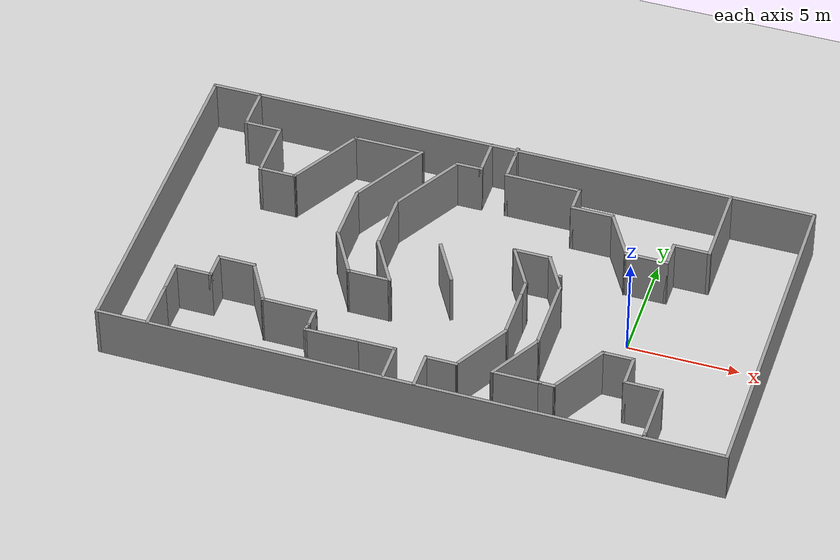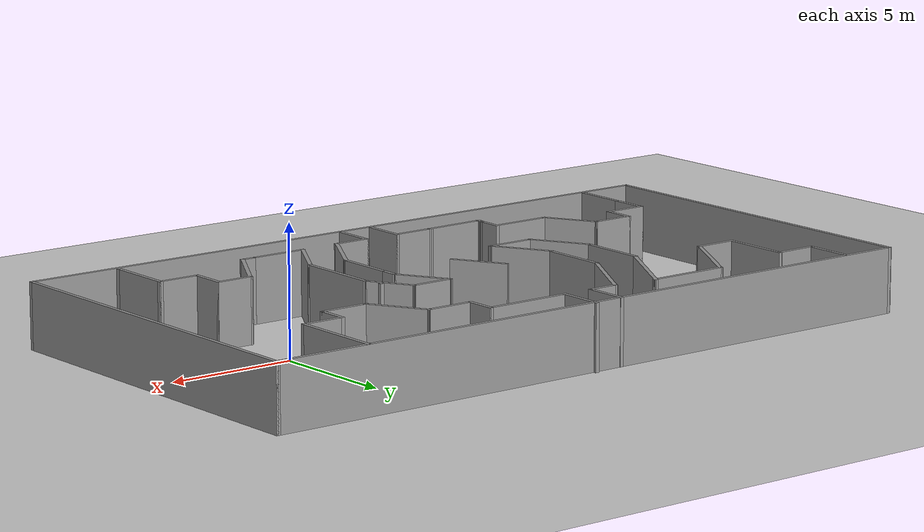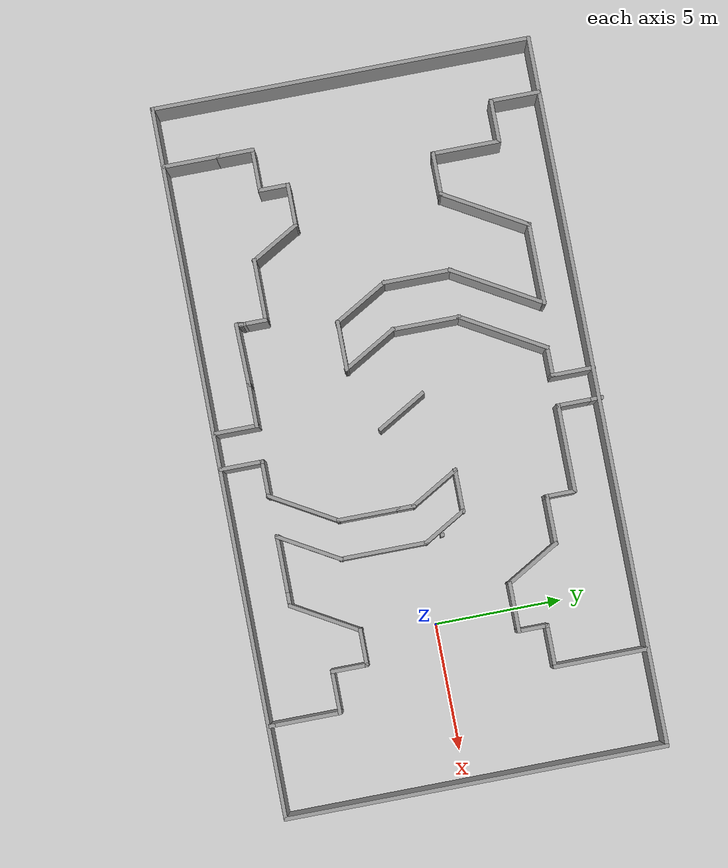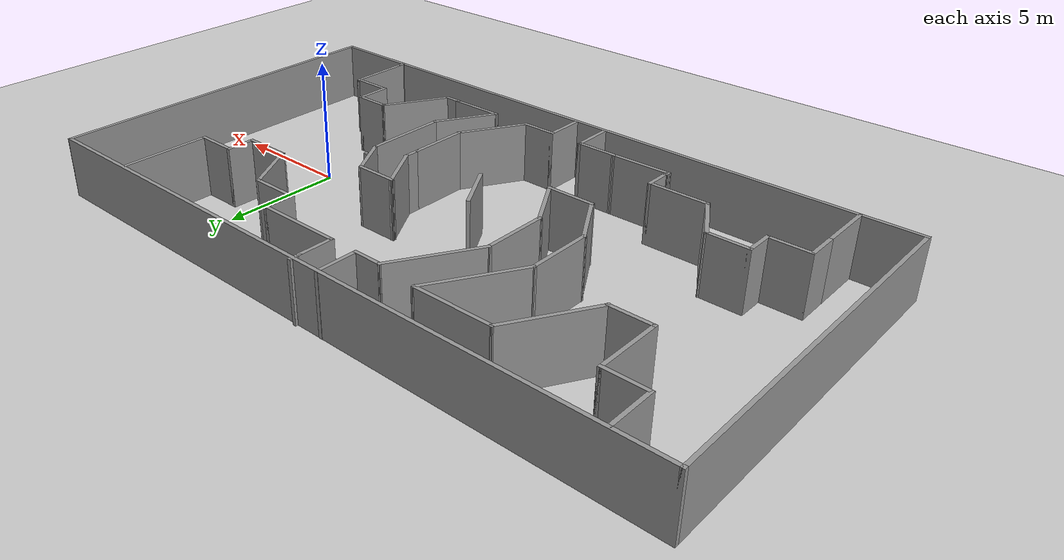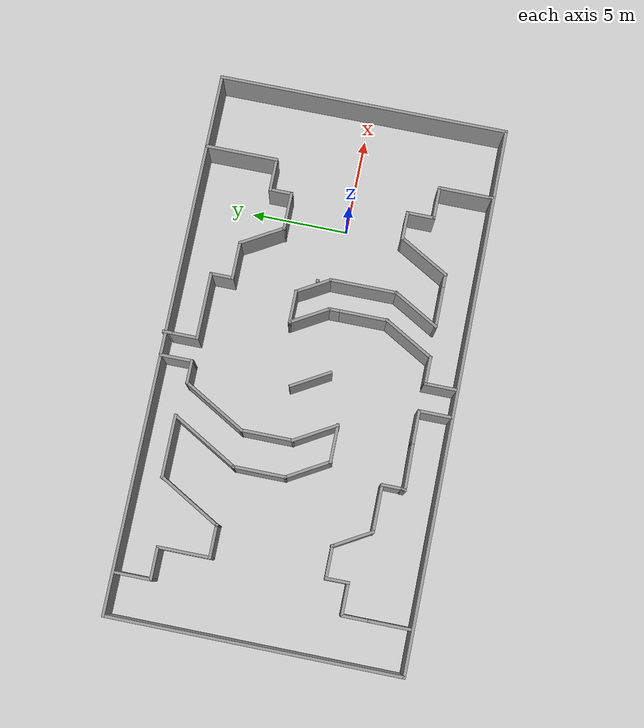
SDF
<sdf version="1.7">
 <world name="default">
  <light name="sun" type="directional">
   <pose>0 0 10 0 -0 0</pose>
   <diffuse>0.8 0.8 0.8 1</diffuse>
   <specular>0.2 0.2 0.2 1</specular>
   <attenuation>
    <range>1000</range>
    <constant>0.9</constant>
    <linear>0.01</linear>
    <quadratic>0.001</quadratic>
   </attenuation>
   <direction>-0.5 0.1 -0.9</direction>
   <spot><inner_angle>0</inner_angle><outer_angle>0</outer_angle><falloff>0</falloff></spot>
  </light>
  <model name="ground_plane">
   <static>1</static>
   <link name="link">
    <collision name="collision">
     <geometry><plane><normal>0 0 1</normal><size>100 100</size></plane></geometry>
     <surface>
      <contact><collide_bitmask>65535</collide_bitmask></contact>
      <friction><ode><mu>100</mu><mu2>50</mu2></ode></friction>
     </surface>
    </collision>
    <visual name="visual">
     <cast_shadows>0</cast_shadows>
     <geometry><plane><normal>0 0 1</normal><size>100 100</size></plane></geometry>
     <material>
      <script><uri>file://media/materials/scripts/gazebo.material</uri><name>Gazebo/Grey</name></script>
     </material>
    </visual>
   </link>
  </model>
  <gravity>0 0 -9.8</gravity>
  <magnetic_field>6e-06 2.3e-05 -4.2e-05</magnetic_field>
  <atmosphere type="adiabatic"/>
  <physics type="ode">
   <max_step_size>0.001</max_step_size>
   <real_time_factor>1</real_time_factor>
   <real_time_update_rate>1000</real_time_update_rate>
  </physics>
  <scene><ambient>0.4 0.4 0.4 1</ambient><background>0.7 0.7 0.7 1</background><shadows>1</shadows></scene>
  <spherical_coordinates>
   <surface_model>EARTH_WGS84</surface_model>
   <latitude_deg>0</latitude_deg>
   <longitude_deg>0</longitude_deg>
   <elevation>0</elevation>
   <heading_deg>0</heading_deg>
  </spherical_coordinates>
  <model name="cubot">
   <link name="Wall_122">
    <pose>0 7.37532 0 0 -0 0</pose>
    <visual name="Wall_122_Visual">
     <pose>0 0 1.25 0 -0 0</pose>
     <geometry><box><size>28 0.15 2.5</size></box></geometry>
     <material>
      <script><uri>file://media/materials/scripts/gazebo.material</uri><name>Gazebo/Grey</name></script>
      <ambient>1 1 1 1</ambient>
      <shader type="pixel"/>
     </material>
     <meta><layer>0</layer></meta>
    </visual>
    <collision name="Wall_122_Collision">
     <pose>0 0 1.25 0 -0 0</pose>
     <geometry><box><size>28 0.15 2.5</size></box></geometry>
     <surface>
      <friction>
       <ode><mu>1</mu><mu2>1</mu2><fdir1>0 0 0</fdir1><slip1>0</slip1><slip2>0</slip2></ode>
       <torsional>
        <coefficient>1</coefficient>
        <patch_radius>0</patch_radius>
        <surface_radius>0</surface_radius>
        <use_patch_radius>1</use_patch_radius>
        <ode><slip>0</slip></ode>
       </torsional>
      </friction>
      <bounce><restitution_coefficient>0</restitution_coefficient><threshold>1e+06</threshold></bounce>
      <contact>
       <collide_without_contact>0</collide_without_contact>
       <collide_without_contact_bitmask>1</collide_without_contact_bitmask>
       <collide_bitmask>1</collide_bitmask>
       <ode>
        <soft_cfm>0</soft_cfm>
        <soft_erp>0.2</soft_erp>
        <kp>1e+13</kp>
        <kd>1</kd>
        <max_vel>0.01</max_vel>
        <min_depth>0</min_depth>
       </ode>
       <bullet>
        <split_impulse>1</split_impulse>
        <split_impulse_penetration_threshold>-0.01</split_impulse_penetration_threshold>
        <soft_cfm>0</soft_cfm>
        <soft_erp>0.2</soft_erp>
        <kp>1e+13</kp>
        <kd>1</kd>
       </bullet>
      </contact>
     </surface>
    </collision>
   </link>
   <link name="Wall_123">
    <pose>13.925 -0.04968 0 0 0 -1.5708</pose>
    <visual name="Wall_123_Visual">
     <pose>0 0 1.25 0 -0 0</pose>
     <geometry><box><size>15 0.15 2.5</size></box></geometry>
     <material>
      <script><uri>file://media/materials/scripts/gazebo.material</uri><name>Gazebo/Grey</name></script>
      <ambient>1 1 1 1</ambient>
      <shader type="pixel"/>
     </material>
     <meta><layer>0</layer></meta>
    </visual>
    <collision name="Wall_123_Collision">
     <pose>0 0 1.25 0 -0 0</pose>
     <geometry><box><size>15 0.15 2.5</size></box></geometry>
     <surface>
      <friction>
       <ode><mu>1</mu><mu2>1</mu2><fdir1>0 0 0</fdir1><slip1>0</slip1><slip2>0</slip2></ode>
       <torsional>
        <coefficient>1</coefficient>
        <patch_radius>0</patch_radius>
        <surface_radius>0</surface_radius>
        <use_patch_radius>1</use_patch_radius>
        <ode><slip>0</slip></ode>
       </torsional>
      </friction>
      <bounce><restitution_coefficient>0</restitution_coefficient><threshold>1e+06</threshold></bounce>
      <contact>
       <collide_without_contact>0</collide_without_contact>
       <collide_without_contact_bitmask>1</collide_without_contact_bitmask>
       <collide_bitmask>1</collide_bitmask>
       <ode>
        <soft_cfm>0</soft_cfm>
        <soft_erp>0.2</soft_erp>
        <kp>1e+13</kp>
        <kd>1</kd>
        <max_vel>0.01</max_vel>
        <min_depth>0</min_depth>
       </ode>
       <bullet>
        <split_impulse>1</split_impulse>
        <split_impulse_penetration_threshold>-0.01</split_impulse_penetration_threshold>
        <soft_cfm>0</soft_cfm>
        <soft_erp>0.2</soft_erp>
        <kp>1e+13</kp>
        <kd>1</kd>
       </bullet>
      </contact>
     </surface>
    </collision>
   </link>
   <link name="Wall_124">
    <pose>0 -7.47468 0 0 -0 3.14159</pose>
    <visual name="Wall_124_Visual">
     <pose>0 0 1.25 0 -0 0</pose>
     <geometry><box><size>28 0.15 2.5</size></box></geometry>
     <material>
      <script><uri>file://media/materials/scripts/gazebo.material</uri><name>Gazebo/Grey</name></script>
      <ambient>1 1 1 1</ambient>
      <shader type="pixel"/>
     </material>
     <meta><layer>0</layer></meta>
    </visual>
    <collision name="Wall_124_Collision">
     <pose>0 0 1.25 0 -0 0</pose>
     <geometry><box><size>28 0.15 2.5</size></box></geometry>
     <surface>
      <friction>
       <ode><mu>1</mu><mu2>1</mu2><fdir1>0 0 0</fdir1><slip1>0</slip1><slip2>0</slip2></ode>
       <torsional>
        <coefficient>1</coefficient>
        <patch_radius>0</patch_radius>
        <surface_radius>0</surface_radius>
        <use_patch_radius>1</use_patch_radius>
        <ode><slip>0</slip></ode>
       </torsional>
      </friction>
      <bounce><restitution_coefficient>0</restitution_coefficient><threshold>1e+06</threshold></bounce>
      <contact>
       <collide_without_contact>0</collide_without_contact>
       <collide_without_contact_bitmask>1</collide_without_contact_bitmask>
       <collide_bitmask>1</collide_bitmask>
       <ode>
        <soft_cfm>0</soft_cfm>
        <soft_erp>0.2</soft_erp>
        <kp>1e+13</kp>
        <kd>1</kd>
        <max_vel>0.01</max_vel>
        <min_depth>0</min_depth>
       </ode>
       <bullet>
        <split_impulse>1</split_impulse>
        <split_impulse_penetration_threshold>-0.01</split_impulse_penetration_threshold>
        <soft_cfm>0</soft_cfm>
        <soft_erp>0.2</soft_erp>
        <kp>1e+13</kp>
        <kd>1</kd>
       </bullet>
      </contact>
     </surface>
    </collision>
   </link>
   <link name="Wall_125">
    <pose>-13.925 -0.04968 0 0 0 -1.5708</pose>
    <visual name="Wall_125_Visual">
     <pose>0 0 1.25 0 -0 0</pose>
     <geometry><box><size>15 0.15 2.5</size></box></geometry>
     <material>
      <script><uri>file://media/materials/scripts/gazebo.material</uri><name>Gazebo/Grey</name></script>
      <ambient>1 1 1 1</ambient>
      <shader type="pixel"/>
     </material>
     <meta><layer>0</layer></meta>
    </visual>
    <collision name="Wall_125_Collision">
     <pose>0 0 1.25 0 -0 0</pose>
     <geometry><box><size>15 0.15 2.5</size></box></geometry>
     <surface>
      <friction>
       <ode><mu>1</mu><mu2>1</mu2><fdir1>0 0 0</fdir1><slip1>0</slip1><slip2>0</slip2></ode>
       <torsional>
        <coefficient>1</coefficient>
        <patch_radius>0</patch_radius>
        <surface_radius>0</surface_radius>
        <use_patch_radius>1</use_patch_radius>
        <ode><slip>0</slip></ode>
       </torsional>
      </friction>
      <bounce><restitution_coefficient>0</restitution_coefficient><threshold>1e+06</threshold></bounce>
      <contact>
       <collide_without_contact>0</collide_without_contact>
       <collide_without_contact_bitmask>1</collide_without_contact_bitmask>
       <collide_bitmask>1</collide_bitmask>
       <ode>
        <soft_cfm>0</soft_cfm>
        <soft_erp>0.2</soft_erp>
        <kp>1e+13</kp>
        <kd>1</kd>
        <max_vel>0.01</max_vel>
        <min_depth>0</min_depth>
       </ode>
       <bullet>
        <split_impulse>1</split_impulse>
        <split_impulse_penetration_threshold>-0.01</split_impulse_penetration_threshold>
        <soft_cfm>0</soft_cfm>
        <soft_erp>0.2</soft_erp>
        <kp>1e+13</kp>
        <kd>1</kd>
       </bullet>
      </contact>
     </surface>
    </collision>
   </link>
   <link name="Wall_126">
    <pose>-11.7781 6.41129 0 0 0 -1.5708</pose>
    <visual name="Wall_126_Visual">
     <pose>0 0 1.25 0 -0 0</pose>
     <geometry><box><size>2 0.15 2.5</size></box></geometry>
     <material>
      <script><uri>file://media/materials/scripts/gazebo.material</uri><name>Gazebo/Grey</name></script>
      <ambient>1 1 1 1</ambient>
      <shader type="pixel"/>
     </material>
     <meta><layer>0</layer></meta>
    </visual>
    <collision name="Wall_126_Collision">
     <pose>0 0 1.25 0 -0 0</pose>
     <geometry><box><size>2 0.15 2.5</size></box></geometry>
     <surface>
      <friction>
       <ode><mu>1</mu><mu2>1</mu2><fdir1>0 0 0</fdir1><slip1>0</slip1><slip2>0</slip2></ode>
       <torsional>
        <coefficient>1</coefficient>
        <patch_radius>0</patch_radius>
        <surface_radius>0</surface_radius>
        <use_patch_radius>1</use_patch_radius>
        <ode><slip>0</slip></ode>
       </torsional>
      </friction>
      <bounce><restitution_coefficient>0</restitution_coefficient><threshold>1e+06</threshold></bounce>
      <contact>
       <collide_without_contact>0</collide_without_contact>
       <collide_without_contact_bitmask>1</collide_without_contact_bitmask>
       <collide_bitmask>1</collide_bitmask>
       <ode>
        <soft_cfm>0</soft_cfm>
        <soft_erp>0.2</soft_erp>
        <kp>1e+13</kp>
        <kd>1</kd>
        <max_vel>0.01</max_vel>
        <min_depth>0</min_depth>
       </ode>
       <bullet>
        <split_impulse>1</split_impulse>
        <split_impulse_penetration_threshold>-0.01</split_impulse_penetration_threshold>
        <soft_cfm>0</soft_cfm>
        <soft_erp>0.2</soft_erp>
        <kp>1e+13</kp>
        <kd>1</kd>
       </bullet>
      </contact>
     </surface>
    </collision>
   </link>
   <link name="Wall_127">
    <pose>-10.9781 5.48629 0 0 -0 0</pose>
    <visual name="Wall_127_Visual">
     <pose>0 0 1.25 0 -0 0</pose>
     <geometry><box><size>1.75 0.15 2.5</size></box></geometry>
     <material>
      <script><uri>file://media/materials/scripts/gazebo.material</uri><name>Gazebo/Grey</name></script>
      <ambient>1 1 1 1</ambient>
      <shader type="pixel"/>
     </material>
     <meta><layer>0</layer></meta>
    </visual>
    <collision name="Wall_127_Collision">
     <pose>0 0 1.25 0 -0 0</pose>
     <geometry><box><size>1.75 0.15 2.5</size></box></geometry>
     <surface>
      <friction>
       <ode><mu>1</mu><mu2>1</mu2><fdir1>0 0 0</fdir1><slip1>0</slip1><slip2>0</slip2></ode>
       <torsional>
        <coefficient>1</coefficient>
        <patch_radius>0</patch_radius>
        <surface_radius>0</surface_radius>
        <use_patch_radius>1</use_patch_radius>
        <ode><slip>0</slip></ode>
       </torsional>
      </friction>
      <bounce><restitution_coefficient>0</restitution_coefficient><threshold>1e+06</threshold></bounce>
      <contact>
       <collide_without_contact>0</collide_without_contact>
       <collide_without_contact_bitmask>1</collide_without_contact_bitmask>
       <collide_bitmask>1</collide_bitmask>
       <ode>
        <soft_cfm>0</soft_cfm>
        <soft_erp>0.2</soft_erp>
        <kp>1e+13</kp>
        <kd>1</kd>
        <max_vel>0.01</max_vel>
        <min_depth>0</min_depth>
       </ode>
       <bullet>
        <split_impulse>1</split_impulse>
        <split_impulse_penetration_threshold>-0.01</split_impulse_penetration_threshold>
        <soft_cfm>0</soft_cfm>
        <soft_erp>0.2</soft_erp>
        <kp>1e+13</kp>
        <kd>1</kd>
       </bullet>
      </contact>
     </surface>
    </collision>
   </link>
   <link name="Wall_128">
    <pose>-10.1781 4.18629 0 0 0 -1.5708</pose>
    <visual name="Wall_128_Visual">
     <pose>0 0 1.25 0 -0 0</pose>
     <geometry><box><size>2.75 0.15 2.5</size></box></geometry>
     <material>
      <script><uri>file://media/materials/scripts/gazebo.material</uri><name>Gazebo/Grey</name></script>
      <ambient>1 1 1 1</ambient>
      <shader type="pixel"/>
     </material>
     <meta><layer>0</layer></meta>
    </visual>
    <collision name="Wall_128_Collision">
     <pose>0 0 1.25 0 -0 0</pose>
     <geometry><box><size>2.75 0.15 2.5</size></box></geometry>
     <surface>
      <friction>
       <ode><mu>1</mu><mu2>1</mu2><fdir1>0 0 0</fdir1><slip1>0</slip1><slip2>0</slip2></ode>
       <torsional>
        <coefficient>1</coefficient>
        <patch_radius>0</patch_radius>
        <surface_radius>0</surface_radius>
        <use_patch_radius>1</use_patch_radius>
        <ode><slip>0</slip></ode>
       </torsional>
      </friction>
      <bounce><restitution_coefficient>0</restitution_coefficient><threshold>1e+06</threshold></bounce>
      <contact>
       <collide_without_contact>0</collide_without_contact>
       <collide_without_contact_bitmask>1</collide_without_contact_bitmask>
       <collide_bitmask>1</collide_bitmask>
       <ode>
        <soft_cfm>0</soft_cfm>
        <soft_erp>0.2</soft_erp>
        <kp>1e+13</kp>
        <kd>1</kd>
        <max_vel>0.01</max_vel>
        <min_depth>0</min_depth>
       </ode>
       <bullet>
        <split_impulse>1</split_impulse>
        <split_impulse_penetration_threshold>-0.01</split_impulse_penetration_threshold>
        <soft_cfm>0</soft_cfm>
        <soft_erp>0.2</soft_erp>
        <kp>1e+13</kp>
        <kd>1</kd>
       </bullet>
      </contact>
     </surface>
    </collision>
   </link>
   <link name="Wall_129">
    <pose>-9.37808 2.88629 0 0 -0 0</pose>
    <visual name="Wall_129_Visual">
     <pose>0 0 1.25 0 -0 0</pose>
     <geometry><box><size>1.75 0.15 2.5</size></box></geometry>
     <material>
      <script><uri>file://media/materials/scripts/gazebo.material</uri><name>Gazebo/Grey</name></script>
      <ambient>1 1 1 1</ambient>
      <shader type="pixel"/>
     </material>
     <meta><layer>0</layer></meta>
    </visual>
    <collision name="Wall_129_Collision">
     <pose>0 0 1.25 0 -0 0</pose>
     <geometry><box><size>1.75 0.15 2.5</size></box></geometry>
     <surface>
      <friction>
       <ode><mu>1</mu><mu2>1</mu2><fdir1>0 0 0</fdir1><slip1>0</slip1><slip2>0</slip2></ode>
       <torsional>
        <coefficient>1</coefficient>
        <patch_radius>0</patch_radius>
        <surface_radius>0</surface_radius>
        <use_patch_radius>1</use_patch_radius>
        <ode><slip>0</slip></ode>
       </torsional>
      </friction>
      <bounce><restitution_coefficient>0</restitution_coefficient><threshold>1e+06</threshold></bounce>
      <contact>
       <collide_without_contact>0</collide_without_contact>
       <collide_without_contact_bitmask>1</collide_without_contact_bitmask>
       <collide_bitmask>1</collide_bitmask>
       <ode>
        <soft_cfm>0</soft_cfm>
        <soft_erp>0.2</soft_erp>
        <kp>1e+13</kp>
        <kd>1</kd>
        <max_vel>0.01</max_vel>
        <min_depth>0</min_depth>
       </ode>
       <bullet>
        <split_impulse>1</split_impulse>
        <split_impulse_penetration_threshold>-0.01</split_impulse_penetration_threshold>
        <soft_cfm>0</soft_cfm>
        <soft_erp>0.2</soft_erp>
        <kp>1e+13</kp>
        <kd>1</kd>
       </bullet>
      </contact>
     </surface>
    </collision>
   </link>
   <link name="Wall_130">
    <pose>-7.67808 4.44513 0 0 -0 1.0472</pose>
    <visual name="Wall_130_Visual">
     <pose>0 0 1.25 0 -0 0</pose>
     <geometry><box><size>3.75 0.15 2.5</size></box></geometry>
     <material>
      <script><uri>file://media/materials/scripts/gazebo.material</uri><name>Gazebo/Grey</name></script>
      <ambient>1 1 1 1</ambient>
      <shader type="pixel"/>
     </material>
     <meta><layer>0</layer></meta>
    </visual>
    <collision name="Wall_130_Collision">
     <pose>0 0 1.25 0 -0 0</pose>
     <geometry><box><size>3.75 0.15 2.5</size></box></geometry>
     <surface>
      <friction>
       <ode><mu>1</mu><mu2>1</mu2><fdir1>0 0 0</fdir1><slip1>0</slip1><slip2>0</slip2></ode>
       <torsional>
        <coefficient>1</coefficient>
        <patch_radius>0</patch_radius>
        <surface_radius>0</surface_radius>
        <use_patch_radius>1</use_patch_radius>
        <ode><slip>0</slip></ode>
       </torsional>
      </friction>
      <bounce><restitution_coefficient>0</restitution_coefficient><threshold>1e+06</threshold></bounce>
      <contact>
       <collide_without_contact>0</collide_without_contact>
       <collide_without_contact_bitmask>1</collide_without_contact_bitmask>
       <collide_bitmask>1</collide_bitmask>
       <ode>
        <soft_cfm>0</soft_cfm>
        <soft_erp>0.2</soft_erp>
        <kp>1e+13</kp>
        <kd>1</kd>
        <max_vel>0.01</max_vel>
        <min_depth>0</min_depth>
       </ode>
       <bullet>
        <split_impulse>1</split_impulse>
        <split_impulse_penetration_threshold>-0.01</split_impulse_penetration_threshold>
        <soft_cfm>0</soft_cfm>
        <soft_erp>0.2</soft_erp>
        <kp>1e+13</kp>
        <kd>1</kd>
       </bullet>
      </contact>
     </surface>
    </collision>
   </link>
   <link name="Wall_131">
    <pose>-5.22808 6.00398 0 0 -0 0</pose>
    <visual name="Wall_131_Visual">
     <pose>0 0 1.25 0 -0 0</pose>
     <geometry><box><size>3.25 0.15 2.5</size></box></geometry>
     <material>
      <script><uri>file://media/materials/scripts/gazebo.material</uri><name>Gazebo/Grey</name></script>
      <ambient>1 1 1 1</ambient>
      <shader type="pixel"/>
     </material>
     <meta><layer>0</layer></meta>
    </visual>
    <collision name="Wall_131_Collision">
     <pose>0 0 1.25 0 -0 0</pose>
     <geometry><box><size>3.25 0.15 2.5</size></box></geometry>
     <surface>
      <friction>
       <ode><mu>1</mu><mu2>1</mu2><fdir1>0 0 0</fdir1><slip1>0</slip1><slip2>0</slip2></ode>
       <torsional>
        <coefficient>1</coefficient>
        <patch_radius>0</patch_radius>
        <surface_radius>0</surface_radius>
        <use_patch_radius>1</use_patch_radius>
        <ode><slip>0</slip></ode>
       </torsional>
      </friction>
      <bounce><restitution_coefficient>0</restitution_coefficient><threshold>1e+06</threshold></bounce>
      <contact>
       <collide_without_contact>0</collide_without_contact>
       <collide_without_contact_bitmask>1</collide_without_contact_bitmask>
       <collide_bitmask>1</collide_bitmask>
       <ode>
        <soft_cfm>0</soft_cfm>
        <soft_erp>0.2</soft_erp>
        <kp>1e+13</kp>
        <kd>1</kd>
        <max_vel>0.01</max_vel>
        <min_depth>0</min_depth>
       </ode>
       <bullet>
        <split_impulse>1</split_impulse>
        <split_impulse_penetration_threshold>-0.01</split_impulse_penetration_threshold>
        <soft_cfm>0</soft_cfm>
        <soft_erp>0.2</soft_erp>
        <kp>1e+13</kp>
        <kd>1</kd>
       </bullet>
      </contact>
     </surface>
    </collision>
   </link>
   <link name="Wall_132">
    <pose>-4.64058 4.33688 0 0 0 -2.0944</pose>
    <visual name="Wall_132_Visual">
     <pose>0 0 1.25 0 -0 0</pose>
     <geometry><box><size>4 0.15 2.5</size></box></geometry>
     <material>
      <script><uri>file://media/materials/scripts/gazebo.material</uri><name>Gazebo/Grey</name></script>
      <ambient>1 1 1 1</ambient>
      <shader type="pixel"/>
     </material>
     <meta><layer>0</layer></meta>
    </visual>
    <collision name="Wall_132_Collision">
     <pose>0 0 1.25 0 -0 0</pose>
     <geometry><box><size>4 0.15 2.5</size></box></geometry>
     <surface>
      <friction>
       <ode><mu>1</mu><mu2>1</mu2><fdir1>0 0 0</fdir1><slip1>0</slip1><slip2>0</slip2></ode>
       <torsional>
        <coefficient>1</coefficient>
        <patch_radius>0</patch_radius>
        <surface_radius>0</surface_radius>
        <use_patch_radius>1</use_patch_radius>
        <ode><slip>0</slip></ode>
       </torsional>
      </friction>
      <bounce><restitution_coefficient>0</restitution_coefficient><threshold>1e+06</threshold></bounce>
      <contact>
       <collide_without_contact>0</collide_without_contact>
       <collide_without_contact_bitmask>1</collide_without_contact_bitmask>
       <collide_bitmask>1</collide_bitmask>
       <ode>
        <soft_cfm>0</soft_cfm>
        <soft_erp>0.2</soft_erp>
        <kp>1e+13</kp>
        <kd>1</kd>
        <max_vel>0.01</max_vel>
        <min_depth>0</min_depth>
       </ode>
       <bullet>
        <split_impulse>1</split_impulse>
        <split_impulse_penetration_threshold>-0.01</split_impulse_penetration_threshold>
        <soft_cfm>0</soft_cfm>
        <soft_erp>0.2</soft_erp>
        <kp>1e+13</kp>
        <kd>1</kd>
       </bullet>
      </contact>
     </surface>
    </collision>
   </link>
   <link name="Wall_133">
    <pose>-5.60308 1.36978 0 0 0 -1.5708</pose>
    <visual name="Wall_133_Visual">
     <pose>0 0 1.25 0 -0 0</pose>
     <geometry><box><size>2.75 0.15 2.5</size></box></geometry>
     <material>
      <script><uri>file://media/materials/scripts/gazebo.material</uri><name>Gazebo/Grey</name></script>
      <ambient>1 1 1 1</ambient>
      <shader type="pixel"/>
     </material>
     <meta><layer>0</layer></meta>
    </visual>
    <collision name="Wall_133_Collision">
     <pose>0 0 1.25 0 -0 0</pose>
     <geometry><box><size>2.75 0.15 2.5</size></box></geometry>
     <surface>
      <friction>
       <ode><mu>1</mu><mu2>1</mu2><fdir1>0 0 0</fdir1><slip1>0</slip1><slip2>0</slip2></ode>
       <torsional>
        <coefficient>1</coefficient>
        <patch_radius>0</patch_radius>
        <surface_radius>0</surface_radius>
        <use_patch_radius>1</use_patch_radius>
        <ode><slip>0</slip></ode>
       </torsional>
      </friction>
      <bounce><restitution_coefficient>0</restitution_coefficient><threshold>1e+06</threshold></bounce>
      <contact>
       <collide_without_contact>0</collide_without_contact>
       <collide_without_contact_bitmask>1</collide_without_contact_bitmask>
       <collide_bitmask>1</collide_bitmask>
       <ode>
        <soft_cfm>0</soft_cfm>
        <soft_erp>0.2</soft_erp>
        <kp>1e+13</kp>
        <kd>1</kd>
        <max_vel>0.01</max_vel>
        <min_depth>0</min_depth>
       </ode>
       <bullet>
        <split_impulse>1</split_impulse>
        <split_impulse_penetration_threshold>-0.01</split_impulse_penetration_threshold>
        <soft_cfm>0</soft_cfm>
        <soft_erp>0.2</soft_erp>
        <kp>1e+13</kp>
        <kd>1</kd>
       </bullet>
      </contact>
     </surface>
    </collision>
   </link>
   <link name="Wall_134">
    <pose>-5.01558 -0.947797 0 0 0 -1.0472</pose>
    <visual name="Wall_134_Visual">
     <pose>0 0 1.25 0 -0 0</pose>
     <geometry><box><size>2.5 0.15 2.5</size></box></geometry>
     <material>
      <script><uri>file://media/materials/scripts/gazebo.material</uri><name>Gazebo/Grey</name></script>
      <ambient>1 1 1 1</ambient>
      <shader type="pixel"/>
     </material>
     <meta><layer>0</layer></meta>
    </visual>
    <collision name="Wall_134_Collision">
     <pose>0 0 1.25 0 -0 0</pose>
     <geometry><box><size>2.5 0.15 2.5</size></box></geometry>
     <surface>
      <friction>
       <ode><mu>1</mu><mu2>1</mu2><fdir1>0 0 0</fdir1><slip1>0</slip1><slip2>0</slip2></ode>
       <torsional>
        <coefficient>1</coefficient>
        <patch_radius>0</patch_radius>
        <surface_radius>0</surface_radius>
        <use_patch_radius>1</use_patch_radius>
        <ode><slip>0</slip></ode>
       </torsional>
      </friction>
      <bounce><restitution_coefficient>0</restitution_coefficient><threshold>1e+06</threshold></bounce>
      <contact>
       <collide_without_contact>0</collide_without_contact>
       <collide_without_contact_bitmask>1</collide_without_contact_bitmask>
       <collide_bitmask>1</collide_bitmask>
       <ode>
        <soft_cfm>0</soft_cfm>
        <soft_erp>0.2</soft_erp>
        <kp>1e+13</kp>
        <kd>1</kd>
        <max_vel>0.01</max_vel>
        <min_depth>0</min_depth>
       </ode>
       <bullet>
        <split_impulse>1</split_impulse>
        <split_impulse_penetration_threshold>-0.01</split_impulse_penetration_threshold>
        <soft_cfm>0</soft_cfm>
        <soft_erp>0.2</soft_erp>
        <kp>1e+13</kp>
        <kd>1</kd>
       </bullet>
      </contact>
     </surface>
    </collision>
   </link>
   <link name="Wall_135">
    <pose>-3.50308 -1.96538 0 0 -0 0</pose>
    <visual name="Wall_135_Visual">
     <pose>0 0 1.25 0 -0 0</pose>
     <geometry><box><size>2 0.15 2.5</size></box></geometry>
     <material>
      <script><uri>file://media/materials/scripts/gazebo.material</uri><name>Gazebo/Grey</name></script>
      <ambient>1 1 1 1</ambient>
      <shader type="pixel"/>
     </material>
     <meta><layer>0</layer></meta>
    </visual>
    <collision name="Wall_135_Collision">
     <pose>0 0 1.25 0 -0 0</pose>
     <geometry><box><size>2 0.15 2.5</size></box></geometry>
     <surface>
      <friction>
       <ode><mu>1</mu><mu2>1</mu2><fdir1>0 0 0</fdir1><slip1>0</slip1><slip2>0</slip2></ode>
       <torsional>
        <coefficient>1</coefficient>
        <patch_radius>0</patch_radius>
        <surface_radius>0</surface_radius>
        <use_patch_radius>1</use_patch_radius>
        <ode><slip>0</slip></ode>
       </torsional>
      </friction>
      <bounce><restitution_coefficient>0</restitution_coefficient><threshold>1e+06</threshold></bounce>
      <contact>
       <collide_without_contact>0</collide_without_contact>
       <collide_without_contact_bitmask>1</collide_without_contact_bitmask>
       <collide_bitmask>1</collide_bitmask>
       <ode>
        <soft_cfm>0</soft_cfm>
        <soft_erp>0.2</soft_erp>
        <kp>1e+13</kp>
        <kd>1</kd>
        <max_vel>0.01</max_vel>
        <min_depth>0</min_depth>
       </ode>
       <bullet>
        <split_impulse>1</split_impulse>
        <split_impulse_penetration_threshold>-0.01</split_impulse_penetration_threshold>
        <soft_cfm>0</soft_cfm>
        <soft_erp>0.2</soft_erp>
        <kp>1e+13</kp>
        <kd>1</kd>
       </bullet>
      </contact>
     </surface>
    </collision>
   </link>
   <link name="Wall_136">
    <pose>-3.16558 -0.947797 0 0 -0 2.0944</pose>
    <visual name="Wall_136_Visual">
     <pose>0 0 1.25 0 -0 0</pose>
     <geometry><box><size>2.5 0.15 2.5</size></box></geometry>
     <material>
      <script><uri>file://media/materials/scripts/gazebo.material</uri><name>Gazebo/Grey</name></script>
      <ambient>1 1 1 1</ambient>
      <shader type="pixel"/>
     </material>
     <meta><layer>0</layer></meta>
    </visual>
    <collision name="Wall_136_Collision">
     <pose>0 0 1.25 0 -0 0</pose>
     <geometry><box><size>2.5 0.15 2.5</size></box></geometry>
     <surface>
      <friction>
       <ode><mu>1</mu><mu2>1</mu2><fdir1>0 0 0</fdir1><slip1>0</slip1><slip2>0</slip2></ode>
       <torsional>
        <coefficient>1</coefficient>
        <patch_radius>0</patch_radius>
        <surface_radius>0</surface_radius>
        <use_patch_radius>1</use_patch_radius>
        <ode><slip>0</slip></ode>
       </torsional>
      </friction>
      <bounce><restitution_coefficient>0</restitution_coefficient><threshold>1e+06</threshold></bounce>
      <contact>
       <collide_without_contact>0</collide_without_contact>
       <collide_without_contact_bitmask>1</collide_without_contact_bitmask>
       <collide_bitmask>1</collide_bitmask>
       <ode>
        <soft_cfm>0</soft_cfm>
        <soft_erp>0.2</soft_erp>
        <kp>1e+13</kp>
        <kd>1</kd>
        <max_vel>0.01</max_vel>
        <min_depth>0</min_depth>
       </ode>
       <bullet>
        <split_impulse>1</split_impulse>
        <split_impulse_penetration_threshold>-0.01</split_impulse_penetration_threshold>
        <soft_cfm>0</soft_cfm>
        <soft_erp>0.2</soft_erp>
        <kp>1e+13</kp>
        <kd>1</kd>
       </bullet>
      </contact>
     </surface>
    </collision>
   </link>
   <link name="Wall_137">
    <pose>-3.75308 1.36978 0 0 -0 1.5708</pose>
    <visual name="Wall_137_Visual">
     <pose>0 0 1.25 0 -0 0</pose>
     <geometry><box><size>2.75 0.15 2.5</size></box></geometry>
     <material>
      <script><uri>file://media/materials/scripts/gazebo.material</uri><name>Gazebo/Grey</name></script>
      <ambient>1 1 1 1</ambient>
      <shader type="pixel"/>
     </material>
     <meta><layer>0</layer></meta>
    </visual>
    <collision name="Wall_137_Collision">
     <pose>0 0 1.25 0 -0 0</pose>
     <geometry><box><size>2.75 0.15 2.5</size></box></geometry>
     <surface>
      <friction>
       <ode><mu>1</mu><mu2>1</mu2><fdir1>0 0 0</fdir1><slip1>0</slip1><slip2>0</slip2></ode>
       <torsional>
        <coefficient>1</coefficient>
        <patch_radius>0</patch_radius>
        <surface_radius>0</surface_radius>
        <use_patch_radius>1</use_patch_radius>
        <ode><slip>0</slip></ode>
       </torsional>
      </friction>
      <bounce><restitution_coefficient>0</restitution_coefficient><threshold>1e+06</threshold></bounce>
      <contact>
       <collide_without_contact>0</collide_without_contact>
       <collide_without_contact_bitmask>1</collide_without_contact_bitmask>
       <collide_bitmask>1</collide_bitmask>
       <ode>
        <soft_cfm>0</soft_cfm>
        <soft_erp>0.2</soft_erp>
        <kp>1e+13</kp>
        <kd>1</kd>
        <max_vel>0.01</max_vel>
        <min_depth>0</min_depth>
       </ode>
       <bullet>
        <split_impulse>1</split_impulse>
        <split_impulse_penetration_threshold>-0.01</split_impulse_penetration_threshold>
        <soft_cfm>0</soft_cfm>
        <soft_erp>0.2</soft_erp>
        <kp>1e+13</kp>
        <kd>1</kd>
       </bullet>
      </contact>
     </surface>
    </collision>
   </link>
   <link name="Wall_138">
    <pose>-2.85308 4.22863 0 0 -0 1.0472</pose>
    <visual name="Wall_138_Visual">
     <pose>0 0 1.25 0 -0 0</pose>
     <geometry><box><size>3.75 0.15 2.5</size></box></geometry>
     <material>
      <script><uri>file://media/materials/scripts/gazebo.material</uri><name>Gazebo/Grey</name></script>
      <ambient>1 1 1 1</ambient>
      <shader type="pixel"/>
     </material>
     <meta><layer>0</layer></meta>
    </visual>
    <collision name="Wall_138_Collision">
     <pose>0 0 1.25 0 -0 0</pose>
     <geometry><box><size>3.75 0.15 2.5</size></box></geometry>
     <surface>
      <friction>
       <ode><mu>1</mu><mu2>1</mu2><fdir1>0 0 0</fdir1><slip1>0</slip1><slip2>0</slip2></ode>
       <torsional>
        <coefficient>1</coefficient>
        <patch_radius>0</patch_radius>
        <surface_radius>0</surface_radius>
        <use_patch_radius>1</use_patch_radius>
        <ode><slip>0</slip></ode>
       </torsional>
      </friction>
      <bounce><restitution_coefficient>0</restitution_coefficient><threshold>1e+06</threshold></bounce>
      <contact>
       <collide_without_contact>0</collide_without_contact>
       <collide_without_contact_bitmask>1</collide_without_contact_bitmask>
       <collide_bitmask>1</collide_bitmask>
       <ode>
        <soft_cfm>0</soft_cfm>
        <soft_erp>0.2</soft_erp>
        <kp>1e+13</kp>
        <kd>1</kd>
        <max_vel>0.01</max_vel>
        <min_depth>0</min_depth>
       </ode>
       <bullet>
        <split_impulse>1</split_impulse>
        <split_impulse_penetration_threshold>-0.01</split_impulse_penetration_threshold>
        <soft_cfm>0</soft_cfm>
        <soft_erp>0.2</soft_erp>
        <kp>1e+13</kp>
        <kd>1</kd>
       </bullet>
      </contact>
     </surface>
    </collision>
   </link>
   <link name="Wall_139">
    <pose>-1.40308 5.78747 0 0 -0 0</pose>
    <visual name="Wall_139_Visual">
     <pose>0 0 1.25 0 -0 0</pose>
     <geometry><box><size>1.25 0.15 2.5</size></box></geometry>
     <material>
      <script><uri>file://media/materials/scripts/gazebo.material</uri><name>Gazebo/Grey</name></script>
      <ambient>1 1 1 1</ambient>
      <shader type="pixel"/>
     </material>
     <meta><layer>0</layer></meta>
    </visual>
    <collision name="Wall_139_Collision">
     <pose>0 0 1.25 0 -0 0</pose>
     <geometry><box><size>1.25 0.15 2.5</size></box></geometry>
     <surface>
      <friction>
       <ode><mu>1</mu><mu2>1</mu2><fdir1>0 0 0</fdir1><slip1>0</slip1><slip2>0</slip2></ode>
       <torsional>
        <coefficient>1</coefficient>
        <patch_radius>0</patch_radius>
        <surface_radius>0</surface_radius>
        <use_patch_radius>1</use_patch_radius>
        <ode><slip>0</slip></ode>
       </torsional>
      </friction>
      <bounce><restitution_coefficient>0</restitution_coefficient><threshold>1e+06</threshold></bounce>
      <contact>
       <collide_without_contact>0</collide_without_contact>
       <collide_without_contact_bitmask>1</collide_without_contact_bitmask>
       <collide_bitmask>1</collide_bitmask>
       <ode>
        <soft_cfm>0</soft_cfm>
        <soft_erp>0.2</soft_erp>
        <kp>1e+13</kp>
        <kd>1</kd>
        <max_vel>0.01</max_vel>
        <min_depth>0</min_depth>
       </ode>
       <bullet>
        <split_impulse>1</split_impulse>
        <split_impulse_penetration_threshold>-0.01</split_impulse_penetration_threshold>
        <soft_cfm>0</soft_cfm>
        <soft_erp>0.2</soft_erp>
        <kp>1e+13</kp>
        <kd>1</kd>
       </bullet>
      </contact>
     </surface>
    </collision>
   </link>
   <link name="Wall_140">
    <pose>-0.853083 6.58747 0 0 -0 1.5708</pose>
    <visual name="Wall_140_Visual">
     <pose>0 0 1.25 0 -0 0</pose>
     <geometry><box><size>1.75 0.15 2.5</size></box></geometry>
     <material>
      <script><uri>file://media/materials/scripts/gazebo.material</uri><name>Gazebo/Grey</name></script>
      <ambient>1 1 1 1</ambient>
      <shader type="pixel"/>
     </material>
     <meta><layer>0</layer></meta>
    </visual>
    <collision name="Wall_140_Collision">
     <pose>0 0 1.25 0 -0 0</pose>
     <geometry><box><size>1.75 0.15 2.5</size></box></geometry>
     <surface>
      <friction>
       <ode><mu>1</mu><mu2>1</mu2><fdir1>0 0 0</fdir1><slip1>0</slip1><slip2>0</slip2></ode>
       <torsional>
        <coefficient>1</coefficient>
        <patch_radius>0</patch_radius>
        <surface_radius>0</surface_radius>
        <use_patch_radius>1</use_patch_radius>
        <ode><slip>0</slip></ode>
       </torsional>
      </friction>
      <bounce><restitution_coefficient>0</restitution_coefficient><threshold>1e+06</threshold></bounce>
      <contact>
       <collide_without_contact>0</collide_without_contact>
       <collide_without_contact_bitmask>1</collide_without_contact_bitmask>
       <collide_bitmask>1</collide_bitmask>
       <ode>
        <soft_cfm>0</soft_cfm>
        <soft_erp>0.2</soft_erp>
        <kp>1e+13</kp>
        <kd>1</kd>
        <max_vel>0.01</max_vel>
        <min_depth>0</min_depth>
       </ode>
       <bullet>
        <split_impulse>1</split_impulse>
        <split_impulse_penetration_threshold>-0.01</split_impulse_penetration_threshold>
        <soft_cfm>0</soft_cfm>
        <soft_erp>0.2</soft_erp>
        <kp>1e+13</kp>
        <kd>1</kd>
       </bullet>
      </contact>
     </surface>
    </collision>
   </link>
   <link name="Wall_141">
    <pose>-11.6355 -6.36384 0 0 -0 1.5708</pose>
    <visual name="Wall_141_Visual">
     <pose>0 0 1.25 0 -0 0</pose>
     <geometry><box><size>2.25 0.15 2.5</size></box></geometry>
     <material>
      <script><uri>file://media/materials/scripts/gazebo.material</uri><name>Gazebo/Grey</name></script>
      <ambient>1 1 1 1</ambient>
      <shader type="pixel"/>
     </material>
     <meta><layer>0</layer></meta>
    </visual>
    <collision name="Wall_141_Collision">
     <pose>0 0 1.25 0 -0 0</pose>
     <geometry><box><size>2.25 0.15 2.5</size></box></geometry>
     <surface>
      <friction>
       <ode><mu>1</mu><mu2>1</mu2><fdir1>0 0 0</fdir1><slip1>0</slip1><slip2>0</slip2></ode>
       <torsional>
        <coefficient>1</coefficient>
        <patch_radius>0</patch_radius>
        <surface_radius>0</surface_radius>
        <use_patch_radius>1</use_patch_radius>
        <ode><slip>0</slip></ode>
       </torsional>
      </friction>
      <bounce><restitution_coefficient>0</restitution_coefficient><threshold>1e+06</threshold></bounce>
      <contact>
       <collide_without_contact>0</collide_without_contact>
       <collide_without_contact_bitmask>1</collide_without_contact_bitmask>
       <collide_bitmask>1</collide_bitmask>
       <ode>
        <soft_cfm>0</soft_cfm>
        <soft_erp>0.2</soft_erp>
        <kp>1e+13</kp>
        <kd>1</kd>
        <max_vel>0.01</max_vel>
        <min_depth>0</min_depth>
       </ode>
       <bullet>
        <split_impulse>1</split_impulse>
        <split_impulse_penetration_threshold>-0.01</split_impulse_penetration_threshold>
        <soft_cfm>0</soft_cfm>
        <soft_erp>0.2</soft_erp>
        <kp>1e+13</kp>
        <kd>1</kd>
       </bullet>
      </contact>
     </surface>
    </collision>
   </link>
   <link name="Wall_142">
    <pose>-11.6355 -4.63884 0 0 -0 1.5708</pose>
    <visual name="Wall_142_Visual">
     <pose>0 0 1.25 0 -0 0</pose>
     <geometry><box><size>1.5 0.15 2.5</size></box></geometry>
     <material>
      <script><uri>file://media/materials/scripts/gazebo.material</uri><name>Gazebo/Grey</name></script>
      <ambient>1 1 1 1</ambient>
      <shader type="pixel"/>
     </material>
     <meta><layer>0</layer></meta>
    </visual>
    <collision name="Wall_142_Collision">
     <pose>0 0 1.25 0 -0 0</pose>
     <geometry><box><size>1.5 0.15 2.5</size></box></geometry>
     <surface>
      <friction>
       <ode><mu>1</mu><mu2>1</mu2><fdir1>0 0 0</fdir1><slip1>0</slip1><slip2>0</slip2></ode>
       <torsional>
        <coefficient>1</coefficient>
        <patch_radius>0</patch_radius>
        <surface_radius>0</surface_radius>
        <use_patch_radius>1</use_patch_radius>
        <ode><slip>0</slip></ode>
       </torsional>
      </friction>
      <bounce><restitution_coefficient>0</restitution_coefficient><threshold>1e+06</threshold></bounce>
      <contact>
       <collide_without_contact>0</collide_without_contact>
       <collide_without_contact_bitmask>1</collide_without_contact_bitmask>
       <collide_bitmask>1</collide_bitmask>
       <ode>
        <soft_cfm>0</soft_cfm>
        <soft_erp>0.2</soft_erp>
        <kp>1e+13</kp>
        <kd>1</kd>
        <max_vel>0.01</max_vel>
        <min_depth>0</min_depth>
       </ode>
       <bullet>
        <split_impulse>1</split_impulse>
        <split_impulse_penetration_threshold>-0.01</split_impulse_penetration_threshold>
        <soft_cfm>0</soft_cfm>
        <soft_erp>0.2</soft_erp>
        <kp>1e+13</kp>
        <kd>1</kd>
       </bullet>
      </contact>
     </surface>
    </collision>
   </link>
   <link name="Wall_143">
    <pose>-10.8355 -3.96384 0 0 -0 0</pose>
    <visual name="Wall_143_Visual">
     <pose>0 0 1.25 0 -0 0</pose>
     <geometry><box><size>1.75 0.15 2.5</size></box></geometry>
     <material>
      <script><uri>file://media/materials/scripts/gazebo.material</uri><name>Gazebo/Grey</name></script>
      <ambient>1 1 1 1</ambient>
      <shader type="pixel"/>
     </material>
     <meta><layer>0</layer></meta>
    </visual>
    <collision name="Wall_143_Collision">
     <pose>0 0 1.25 0 -0 0</pose>
     <geometry><box><size>1.75 0.15 2.5</size></box></geometry>
     <surface>
      <friction>
       <ode><mu>1</mu><mu2>1</mu2><fdir1>0 0 0</fdir1><slip1>0</slip1><slip2>0</slip2></ode>
       <torsional>
        <coefficient>1</coefficient>
        <patch_radius>0</patch_radius>
        <surface_radius>0</surface_radius>
        <use_patch_radius>1</use_patch_radius>
        <ode><slip>0</slip></ode>
       </torsional>
      </friction>
      <bounce><restitution_coefficient>0</restitution_coefficient><threshold>1e+06</threshold></bounce>
      <contact>
       <collide_without_contact>0</collide_without_contact>
       <collide_without_contact_bitmask>1</collide_without_contact_bitmask>
       <collide_bitmask>1</collide_bitmask>
       <ode>
        <soft_cfm>0</soft_cfm>
        <soft_erp>0.2</soft_erp>
        <kp>1e+13</kp>
        <kd>1</kd>
        <max_vel>0.01</max_vel>
        <min_depth>0</min_depth>
       </ode>
       <bullet>
        <split_impulse>1</split_impulse>
        <split_impulse_penetration_threshold>-0.01</split_impulse_penetration_threshold>
        <soft_cfm>0</soft_cfm>
        <soft_erp>0.2</soft_erp>
        <kp>1e+13</kp>
        <kd>1</kd>
       </bullet>
      </contact>
     </surface>
    </collision>
   </link>
   <link name="Wall_144">
    <pose>-10.0355 -3.41384 0 0 -0 1.5708</pose>
    <visual name="Wall_144_Visual">
     <pose>0 0 1.25 0 -0 0</pose>
     <geometry><box><size>1.25 0.15 2.5</size></box></geometry>
     <material>
      <script><uri>file://media/materials/scripts/gazebo.material</uri><name>Gazebo/Grey</name></script>
      <ambient>1 1 1 1</ambient>
      <shader type="pixel"/>
     </material>
     <meta><layer>0</layer></meta>
    </visual>
    <collision name="Wall_144_Collision">
     <pose>0 0 1.25 0 -0 0</pose>
     <geometry><box><size>1.25 0.15 2.5</size></box></geometry>
     <surface>
      <friction>
       <ode><mu>1</mu><mu2>1</mu2><fdir1>0 0 0</fdir1><slip1>0</slip1><slip2>0</slip2></ode>
       <torsional>
        <coefficient>1</coefficient>
        <patch_radius>0</patch_radius>
        <surface_radius>0</surface_radius>
        <use_patch_radius>1</use_patch_radius>
        <ode><slip>0</slip></ode>
       </torsional>
      </friction>
      <bounce><restitution_coefficient>0</restitution_coefficient><threshold>1e+06</threshold></bounce>
      <contact>
       <collide_without_contact>0</collide_without_contact>
       <collide_without_contact_bitmask>1</collide_without_contact_bitmask>
       <collide_bitmask>1</collide_bitmask>
       <ode>
        <soft_cfm>0</soft_cfm>
        <soft_erp>0.2</soft_erp>
        <kp>1e+13</kp>
        <kd>1</kd>
        <max_vel>0.01</max_vel>
        <min_depth>0</min_depth>
       </ode>
       <bullet>
        <split_impulse>1</split_impulse>
        <split_impulse_penetration_threshold>-0.01</split_impulse_penetration_threshold>
        <soft_cfm>0</soft_cfm>
        <soft_erp>0.2</soft_erp>
        <kp>1e+13</kp>
        <kd>1</kd>
       </bullet>
      </contact>
     </surface>
    </collision>
   </link>
   <link name="Wall_145">
    <pose>-9.2355 -2.86384 0 0 -0 0</pose>
    <visual name="Wall_145_Visual">
     <pose>0 0 1.25 0 -0 0</pose>
     <geometry><box><size>1.75 0.15 2.5</size></box></geometry>
     <material>
      <script><uri>file://media/materials/scripts/gazebo.material</uri><name>Gazebo/Grey</name></script>
      <ambient>1 1 1 1</ambient>
      <shader type="pixel"/>
     </material>
     <meta><layer>0</layer></meta>
    </visual>
    <collision name="Wall_145_Collision">
     <pose>0 0 1.25 0 -0 0</pose>
     <geometry><box><size>1.75 0.15 2.5</size></box></geometry>
     <surface>
      <friction>
       <ode><mu>1</mu><mu2>1</mu2><fdir1>0 0 0</fdir1><slip1>0</slip1><slip2>0</slip2></ode>
       <torsional>
        <coefficient>1</coefficient>
        <patch_radius>0</patch_radius>
        <surface_radius>0</surface_radius>
        <use_patch_radius>1</use_patch_radius>
        <ode><slip>0</slip></ode>
       </torsional>
      </friction>
      <bounce><restitution_coefficient>0</restitution_coefficient><threshold>1e+06</threshold></bounce>
      <contact>
       <collide_without_contact>0</collide_without_contact>
       <collide_without_contact_bitmask>1</collide_without_contact_bitmask>
       <collide_bitmask>1</collide_bitmask>
       <ode>
        <soft_cfm>0</soft_cfm>
        <soft_erp>0.2</soft_erp>
        <kp>1e+13</kp>
        <kd>1</kd>
        <max_vel>0.01</max_vel>
        <min_depth>0</min_depth>
       </ode>
       <bullet>
        <split_impulse>1</split_impulse>
        <split_impulse_penetration_threshold>-0.01</split_impulse_penetration_threshold>
        <soft_cfm>0</soft_cfm>
        <soft_erp>0.2</soft_erp>
        <kp>1e+13</kp>
        <kd>1</kd>
       </bullet>
      </contact>
     </surface>
    </collision>
   </link>
   <link name="Wall_146">
    <pose>-7.9105 -3.77316 0 0 0 -1.0472</pose>
    <visual name="Wall_146_Visual">
     <pose>0 0 1.25 0 -0 0</pose>
     <geometry><box><size>2.25 0.15 2.5</size></box></geometry>
     <material>
      <script><uri>file://media/materials/scripts/gazebo.material</uri><name>Gazebo/Grey</name></script>
      <ambient>1 1 1 1</ambient>
      <shader type="pixel"/>
     </material>
     <meta><layer>0</layer></meta>
    </visual>
    <collision name="Wall_146_Collision">
     <pose>0 0 1.25 0 -0 0</pose>
     <geometry><box><size>2.25 0.15 2.5</size></box></geometry>
     <surface>
      <friction>
       <ode><mu>1</mu><mu2>1</mu2><fdir1>0 0 0</fdir1><slip1>0</slip1><slip2>0</slip2></ode>
       <torsional>
        <coefficient>1</coefficient>
        <patch_radius>0</patch_radius>
        <surface_radius>0</surface_radius>
        <use_patch_radius>1</use_patch_radius>
        <ode><slip>0</slip></ode>
       </torsional>
      </friction>
      <bounce><restitution_coefficient>0</restitution_coefficient><threshold>1e+06</threshold></bounce>
      <contact>
       <collide_without_contact>0</collide_without_contact>
       <collide_without_contact_bitmask>1</collide_without_contact_bitmask>
       <collide_bitmask>1</collide_bitmask>
       <ode>
        <soft_cfm>0</soft_cfm>
        <soft_erp>0.2</soft_erp>
        <kp>1e+13</kp>
        <kd>1</kd>
        <max_vel>0.01</max_vel>
        <min_depth>0</min_depth>
       </ode>
       <bullet>
        <split_impulse>1</split_impulse>
        <split_impulse_penetration_threshold>-0.01</split_impulse_penetration_threshold>
        <soft_cfm>0</soft_cfm>
        <soft_erp>0.2</soft_erp>
        <kp>1e+13</kp>
        <kd>1</kd>
       </bullet>
      </contact>
     </surface>
    </collision>
   </link>
   <link name="Wall_147">
    <pose>-6.2105 -4.68249 0 0 -0 0</pose>
    <visual name="Wall_147_Visual">
     <pose>0 0 1.25 0 -0 0</pose>
     <geometry><box><size>2.5 0.15 2.5</size></box></geometry>
     <material>
      <script><uri>file://media/materials/scripts/gazebo.material</uri><name>Gazebo/Grey</name></script>
      <ambient>1 1 1 1</ambient>
      <shader type="pixel"/>
     </material>
     <meta><layer>0</layer></meta>
    </visual>
    <collision name="Wall_147_Collision">
     <pose>0 0 1.25 0 -0 0</pose>
     <geometry><box><size>2.5 0.15 2.5</size></box></geometry>
     <surface>
      <friction>
       <ode><mu>1</mu><mu2>1</mu2><fdir1>0 0 0</fdir1><slip1>0</slip1><slip2>0</slip2></ode>
       <torsional>
        <coefficient>1</coefficient>
        <patch_radius>0</patch_radius>
        <surface_radius>0</surface_radius>
        <use_patch_radius>1</use_patch_radius>
        <ode><slip>0</slip></ode>
       </torsional>
      </friction>
      <bounce><restitution_coefficient>0</restitution_coefficient><threshold>1e+06</threshold></bounce>
      <contact>
       <collide_without_contact>0</collide_without_contact>
       <collide_without_contact_bitmask>1</collide_without_contact_bitmask>
       <collide_bitmask>1</collide_bitmask>
       <ode>
        <soft_cfm>0</soft_cfm>
        <soft_erp>0.2</soft_erp>
        <kp>1e+13</kp>
        <kd>1</kd>
        <max_vel>0.01</max_vel>
        <min_depth>0</min_depth>
       </ode>
       <bullet>
        <split_impulse>1</split_impulse>
        <split_impulse_penetration_threshold>-0.01</split_impulse_penetration_threshold>
        <soft_cfm>0</soft_cfm>
        <soft_erp>0.2</soft_erp>
        <kp>1e+13</kp>
        <kd>1</kd>
       </bullet>
      </contact>
     </surface>
    </collision>
   </link>
   <link name="Wall_148">
    <pose>-1.8855 -5.78249 0 0 -0 0</pose>
    <visual name="Wall_148_Visual">
     <pose>0 0 1.25 0 -0 0</pose>
     <geometry><box><size>1.75 0.15 2.5</size></box></geometry>
     <material>
      <script><uri>file://media/materials/scripts/gazebo.material</uri><name>Gazebo/Grey</name></script>
      <ambient>1 1 1 1</ambient>
      <shader type="pixel"/>
     </material>
     <meta><layer>0</layer></meta>
    </visual>
    <collision name="Wall_148_Collision">
     <pose>0 0 1.25 0 -0 0</pose>
     <geometry><box><size>1.75 0.15 2.5</size></box></geometry>
     <surface>
      <friction>
       <ode><mu>1</mu><mu2>1</mu2><fdir1>0 0 0</fdir1><slip1>0</slip1><slip2>0</slip2></ode>
       <torsional>
        <coefficient>1</coefficient>
        <patch_radius>0</patch_radius>
        <surface_radius>0</surface_radius>
        <use_patch_radius>1</use_patch_radius>
        <ode><slip>0</slip></ode>
       </torsional>
      </friction>
      <bounce><restitution_coefficient>0</restitution_coefficient><threshold>1e+06</threshold></bounce>
      <contact>
       <collide_without_contact>0</collide_without_contact>
       <collide_without_contact_bitmask>1</collide_without_contact_bitmask>
       <collide_bitmask>1</collide_bitmask>
       <ode>
        <soft_cfm>0</soft_cfm>
        <soft_erp>0.2</soft_erp>
        <kp>1e+13</kp>
        <kd>1</kd>
        <max_vel>0.01</max_vel>
        <min_depth>0</min_depth>
       </ode>
       <bullet>
        <split_impulse>1</split_impulse>
        <split_impulse_penetration_threshold>-0.01</split_impulse_penetration_threshold>
        <soft_cfm>0</soft_cfm>
        <soft_erp>0.2</soft_erp>
        <kp>1e+13</kp>
        <kd>1</kd>
       </bullet>
      </contact>
     </surface>
    </collision>
   </link>
   <link name="Wall_149">
    <pose>-1.0855 -6.58249 0 0 0 -1.5708</pose>
    <visual name="Wall_149_Visual">
     <pose>0 0 1.25 0 -0 0</pose>
     <geometry><box><size>1.75 0.15 2.5</size></box></geometry>
     <material>
      <script><uri>file://media/materials/scripts/gazebo.material</uri><name>Gazebo/Grey</name></script>
      <ambient>1 1 1 1</ambient>
      <shader type="pixel"/>
     </material>
     <meta><layer>0</layer></meta>
    </visual>
    <collision name="Wall_149_Collision">
     <pose>0 0 1.25 0 -0 0</pose>
     <geometry><box><size>1.75 0.15 2.5</size></box></geometry>
     <surface>
      <friction>
       <ode><mu>1</mu><mu2>1</mu2><fdir1>0 0 0</fdir1><slip1>0</slip1><slip2>0</slip2></ode>
       <torsional>
        <coefficient>1</coefficient>
        <patch_radius>0</patch_radius>
        <surface_radius>0</surface_radius>
        <use_patch_radius>1</use_patch_radius>
        <ode><slip>0</slip></ode>
       </torsional>
      </friction>
      <bounce><restitution_coefficient>0</restitution_coefficient><threshold>1e+06</threshold></bounce>
      <contact>
       <collide_without_contact>0</collide_without_contact>
       <collide_without_contact_bitmask>1</collide_without_contact_bitmask>
       <collide_bitmask>1</collide_bitmask>
       <ode>
        <soft_cfm>0</soft_cfm>
        <soft_erp>0.2</soft_erp>
        <kp>1e+13</kp>
        <kd>1</kd>
        <max_vel>0.01</max_vel>
        <min_depth>0</min_depth>
       </ode>
       <bullet>
        <split_impulse>1</split_impulse>
        <split_impulse_penetration_threshold>-0.01</split_impulse_penetration_threshold>
        <soft_cfm>0</soft_cfm>
        <soft_erp>0.2</soft_erp>
        <kp>1e+13</kp>
        <kd>1</kd>
       </bullet>
      </contact>
     </surface>
    </collision>
   </link>
   <link name="Wall_150">
    <pose>-5.0355 -5.10749 0 0 0 -1.5708</pose>
    <visual name="Wall_150_Visual">
     <pose>0 0 1.25 0 -0 0</pose>
     <geometry><box><size>1 0.15 2.5</size></box></geometry>
     <material>
      <script><uri>file://media/materials/scripts/gazebo.material</uri><name>Gazebo/Grey</name></script>
      <ambient>1 1 1 1</ambient>
      <shader type="pixel"/>
     </material>
     <meta><layer>0</layer></meta>
    </visual>
    <collision name="Wall_150_Collision">
     <pose>0 0 1.25 0 -0 0</pose>
     <geometry><box><size>1 0.15 2.5</size></box></geometry>
     <surface>
      <friction>
       <ode><mu>1</mu><mu2>1</mu2><fdir1>0 0 0</fdir1><slip1>0</slip1><slip2>0</slip2></ode>
       <torsional>
        <coefficient>1</coefficient>
        <patch_radius>0</patch_radius>
        <surface_radius>0</surface_radius>
        <use_patch_radius>1</use_patch_radius>
        <ode><slip>0</slip></ode>
       </torsional>
      </friction>
      <bounce><restitution_coefficient>0</restitution_coefficient><threshold>1e+06</threshold></bounce>
      <contact>
       <collide_without_contact>0</collide_without_contact>
       <collide_without_contact_bitmask>1</collide_without_contact_bitmask>
       <collide_bitmask>1</collide_bitmask>
       <ode>
        <soft_cfm>0</soft_cfm>
        <soft_erp>0.2</soft_erp>
        <kp>1e+13</kp>
        <kd>1</kd>
        <max_vel>0.01</max_vel>
        <min_depth>0</min_depth>
       </ode>
       <bullet>
        <split_impulse>1</split_impulse>
        <split_impulse_penetration_threshold>-0.01</split_impulse_penetration_threshold>
        <soft_cfm>0</soft_cfm>
        <soft_erp>0.2</soft_erp>
        <kp>1e+13</kp>
        <kd>1</kd>
       </bullet>
      </contact>
     </surface>
    </collision>
   </link>
   <link name="Wall_151">
    <pose>-5.0355 -5.58249 0 0 0 -1.5708</pose>
    <visual name="Wall_151_Visual">
     <pose>0 0 1.25 0 -0 0</pose>
     <geometry><box><size>0.25 0.15 2.5</size></box></geometry>
     <material>
      <script><uri>file://media/materials/scripts/gazebo.material</uri><name>Gazebo/Grey</name></script>
      <ambient>1 1 1 1</ambient>
      <shader type="pixel"/>
     </material>
     <meta><layer>0</layer></meta>
    </visual>
    <collision name="Wall_151_Collision">
     <pose>0 0 1.25 0 -0 0</pose>
     <geometry><box><size>0.25 0.15 2.5</size></box></geometry>
     <surface>
      <friction>
       <ode><mu>1</mu><mu2>1</mu2><fdir1>0 0 0</fdir1><slip1>0</slip1><slip2>0</slip2></ode>
       <torsional>
        <coefficient>1</coefficient>
        <patch_radius>0</patch_radius>
        <surface_radius>0</surface_radius>
        <use_patch_radius>1</use_patch_radius>
        <ode><slip>0</slip></ode>
       </torsional>
      </friction>
      <bounce><restitution_coefficient>0</restitution_coefficient><threshold>1e+06</threshold></bounce>
      <contact>
       <collide_without_contact>0</collide_without_contact>
       <collide_without_contact_bitmask>1</collide_without_contact_bitmask>
       <collide_bitmask>1</collide_bitmask>
       <ode>
        <soft_cfm>0</soft_cfm>
        <soft_erp>0.2</soft_erp>
        <kp>1e+13</kp>
        <kd>1</kd>
        <max_vel>0.01</max_vel>
        <min_depth>0</min_depth>
       </ode>
       <bullet>
        <split_impulse>1</split_impulse>
        <split_impulse_penetration_threshold>-0.01</split_impulse_penetration_threshold>
        <soft_cfm>0</soft_cfm>
        <soft_erp>0.2</soft_erp>
        <kp>1e+13</kp>
        <kd>1</kd>
       </bullet>
      </contact>
     </surface>
    </collision>
   </link>
   <link name="Wall_152">
    <pose>-5.04844 -5.68079 0 0 0 -1.8326</pose>
    <visual name="Wall_152_Visual">
     <pose>0 0 1.25 0 -0 0</pose>
     <geometry><box><size>0.25 0.15 2.5</size></box></geometry>
     <material>
      <script><uri>file://media/materials/scripts/gazebo.material</uri><name>Gazebo/Grey</name></script>
      <ambient>1 1 1 1</ambient>
      <shader type="pixel"/>
     </material>
     <meta><layer>0</layer></meta>
    </visual>
    <collision name="Wall_152_Collision">
     <pose>0 0 1.25 0 -0 0</pose>
     <geometry><box><size>0.25 0.15 2.5</size></box></geometry>
     <surface>
      <friction>
       <ode><mu>1</mu><mu2>1</mu2><fdir1>0 0 0</fdir1><slip1>0</slip1><slip2>0</slip2></ode>
       <torsional>
        <coefficient>1</coefficient>
        <patch_radius>0</patch_radius>
        <surface_radius>0</surface_radius>
        <use_patch_radius>1</use_patch_radius>
        <ode><slip>0</slip></ode>
       </torsional>
      </friction>
      <bounce><restitution_coefficient>0</restitution_coefficient><threshold>1e+06</threshold></bounce>
      <contact>
       <collide_without_contact>0</collide_without_contact>
       <collide_without_contact_bitmask>1</collide_without_contact_bitmask>
       <collide_bitmask>1</collide_bitmask>
       <ode>
        <soft_cfm>0</soft_cfm>
        <soft_erp>0.2</soft_erp>
        <kp>1e+13</kp>
        <kd>1</kd>
        <max_vel>0.01</max_vel>
        <min_depth>0</min_depth>
       </ode>
       <bullet>
        <split_impulse>1</split_impulse>
        <split_impulse_penetration_threshold>-0.01</split_impulse_penetration_threshold>
        <soft_cfm>0</soft_cfm>
        <soft_erp>0.2</soft_erp>
        <kp>1e+13</kp>
        <kd>1</kd>
       </bullet>
      </contact>
     </surface>
    </collision>
   </link>
   <link name="Wall_153">
    <pose>-5.06138 -5.77908 0 0 0 -1.5708</pose>
    <visual name="Wall_153_Visual">
     <pose>0 0 1.25 0 -0 0</pose>
     <geometry><box><size>0.25 0.15 2.5</size></box></geometry>
     <material>
      <script><uri>file://media/materials/scripts/gazebo.material</uri><name>Gazebo/Grey</name></script>
      <ambient>1 1 1 1</ambient>
      <shader type="pixel"/>
     </material>
     <meta><layer>0</layer></meta>
    </visual>
    <collision name="Wall_153_Collision">
     <pose>0 0 1.25 0 -0 0</pose>
     <geometry><box><size>0.25 0.15 2.5</size></box></geometry>
     <surface>
      <friction>
       <ode><mu>1</mu><mu2>1</mu2><fdir1>0 0 0</fdir1><slip1>0</slip1><slip2>0</slip2></ode>
       <torsional>
        <coefficient>1</coefficient>
        <patch_radius>0</patch_radius>
        <surface_radius>0</surface_radius>
        <use_patch_radius>1</use_patch_radius>
        <ode><slip>0</slip></ode>
       </torsional>
      </friction>
      <bounce><restitution_coefficient>0</restitution_coefficient><threshold>1e+06</threshold></bounce>
      <contact>
       <collide_without_contact>0</collide_without_contact>
       <collide_without_contact_bitmask>1</collide_without_contact_bitmask>
       <collide_bitmask>1</collide_bitmask>
       <ode>
        <soft_cfm>0</soft_cfm>
        <soft_erp>0.2</soft_erp>
        <kp>1e+13</kp>
        <kd>1</kd>
        <max_vel>0.01</max_vel>
        <min_depth>0</min_depth>
       </ode>
       <bullet>
        <split_impulse>1</split_impulse>
        <split_impulse_penetration_threshold>-0.01</split_impulse_penetration_threshold>
        <soft_cfm>0</soft_cfm>
        <soft_erp>0.2</soft_erp>
        <kp>1e+13</kp>
        <kd>1</kd>
       </bullet>
      </contact>
     </surface>
    </collision>
   </link>
   <link name="Wall_154">
    <pose>-3.87344 -5.80579 0 0 -0 0.019608</pose>
    <visual name="Wall_154_Visual">
     <pose>0 0 1.25 0 -0 0</pose>
     <geometry><box><size>2.52634 0.15 2.5</size></box></geometry>
     <material>
      <script><uri>file://media/materials/scripts/gazebo.material</uri><name>Gazebo/Grey</name></script>
      <ambient>1 1 1 1</ambient>
      <shader type="pixel"/>
     </material>
     <meta><layer>0</layer></meta>
    </visual>
    <collision name="Wall_154_Collision">
     <pose>0 0 1.25 0 -0 0</pose>
     <geometry><box><size>2.52634 0.15 2.5</size></box></geometry>
     <surface>
      <friction>
       <ode><mu>1</mu><mu2>1</mu2><fdir1>0 0 0</fdir1><slip1>0</slip1><slip2>0</slip2></ode>
       <torsional>
        <coefficient>1</coefficient>
        <patch_radius>0</patch_radius>
        <surface_radius>0</surface_radius>
        <use_patch_radius>1</use_patch_radius>
        <ode><slip>0</slip></ode>
       </torsional>
      </friction>
      <bounce><restitution_coefficient>0</restitution_coefficient><threshold>1e+06</threshold></bounce>
      <contact>
       <collide_without_contact>0</collide_without_contact>
       <collide_without_contact_bitmask>1</collide_without_contact_bitmask>
       <collide_bitmask>1</collide_bitmask>
       <ode>
        <soft_cfm>0</soft_cfm>
        <soft_erp>0.2</soft_erp>
        <kp>1e+13</kp>
        <kd>1</kd>
        <max_vel>0.01</max_vel>
        <min_depth>0</min_depth>
       </ode>
       <bullet>
        <split_impulse>1</split_impulse>
        <split_impulse_penetration_threshold>-0.01</split_impulse_penetration_threshold>
        <soft_cfm>0</soft_cfm>
        <soft_erp>0.2</soft_erp>
        <kp>1e+13</kp>
        <kd>1</kd>
       </bullet>
      </contact>
     </surface>
    </collision>
   </link>
   <link name="Wall_155">
    <pose>0.339347 6.44968 0 0 -0 1.5708</pose>
    <visual name="Wall_155_Visual">
     <pose>0 0 1.25 0 -0 0</pose>
     <geometry><box><size>1.5 0.15 2.5</size></box></geometry>
     <material>
      <script><uri>file://media/materials/scripts/gazebo.material</uri><name>Gazebo/Grey</name></script>
      <ambient>1 1 1 1</ambient>
      <shader type="pixel"/>
     </material>
     <meta><layer>0</layer></meta>
    </visual>
    <collision name="Wall_155_Collision">
     <pose>0 0 1.25 0 -0 0</pose>
     <geometry><box><size>1.5 0.15 2.5</size></box></geometry>
     <surface>
      <friction>
       <ode><mu>1</mu><mu2>1</mu2><fdir1>0 0 0</fdir1><slip1>0</slip1><slip2>0</slip2></ode>
       <torsional>
        <coefficient>1</coefficient>
        <patch_radius>0</patch_radius>
        <surface_radius>0</surface_radius>
        <use_patch_radius>1</use_patch_radius>
        <ode><slip>0</slip></ode>
       </torsional>
      </friction>
      <bounce><restitution_coefficient>0</restitution_coefficient><threshold>1e+06</threshold></bounce>
      <contact>
       <collide_without_contact>0</collide_without_contact>
       <collide_without_contact_bitmask>1</collide_without_contact_bitmask>
       <collide_bitmask>1</collide_bitmask>
       <ode>
        <soft_cfm>0</soft_cfm>
        <soft_erp>0.2</soft_erp>
        <kp>1e+13</kp>
        <kd>1</kd>
        <max_vel>0.01</max_vel>
        <min_depth>0</min_depth>
       </ode>
       <bullet>
        <split_impulse>1</split_impulse>
        <split_impulse_penetration_threshold>-0.01</split_impulse_penetration_threshold>
        <soft_cfm>0</soft_cfm>
        <soft_erp>0.2</soft_erp>
        <kp>1e+13</kp>
        <kd>1</kd>
       </bullet>
      </contact>
     </surface>
    </collision>
   </link>
   <link name="Wall_156">
    <pose>0.339347 7.29968 0 0 -0 1.5708</pose>
    <visual name="Wall_156_Visual">
     <pose>0 0 1.25 0 -0 0</pose>
     <geometry><box><size>0.5 0.15 2.5</size></box></geometry>
     <material>
      <script><uri>file://media/materials/scripts/gazebo.material</uri><name>Gazebo/Grey</name></script>
      <ambient>1 1 1 1</ambient>
      <shader type="pixel"/>
     </material>
     <meta><layer>0</layer></meta>
    </visual>
    <collision name="Wall_156_Collision">
     <pose>0 0 1.25 0 -0 0</pose>
     <geometry><box><size>0.5 0.15 2.5</size></box></geometry>
     <surface>
      <friction>
       <ode><mu>1</mu><mu2>1</mu2><fdir1>0 0 0</fdir1><slip1>0</slip1><slip2>0</slip2></ode>
       <torsional>
        <coefficient>1</coefficient>
        <patch_radius>0</patch_radius>
        <surface_radius>0</surface_radius>
        <use_patch_radius>1</use_patch_radius>
        <ode><slip>0</slip></ode>
       </torsional>
      </friction>
      <bounce><restitution_coefficient>0</restitution_coefficient><threshold>1e+06</threshold></bounce>
      <contact>
       <collide_without_contact>0</collide_without_contact>
       <collide_without_contact_bitmask>1</collide_without_contact_bitmask>
       <collide_bitmask>1</collide_bitmask>
       <ode>
        <soft_cfm>0</soft_cfm>
        <soft_erp>0.2</soft_erp>
        <kp>1e+13</kp>
        <kd>1</kd>
        <max_vel>0.01</max_vel>
        <min_depth>0</min_depth>
       </ode>
       <bullet>
        <split_impulse>1</split_impulse>
        <split_impulse_penetration_threshold>-0.01</split_impulse_penetration_threshold>
        <soft_cfm>0</soft_cfm>
        <soft_erp>0.2</soft_erp>
        <kp>1e+13</kp>
        <kd>1</kd>
       </bullet>
      </contact>
     </surface>
    </collision>
   </link>
   <link name="Wall_157">
    <pose>2.01435 5.77468 0 0 -0 0</pose>
    <visual name="Wall_157_Visual">
     <pose>0 0 1.25 0 -0 0</pose>
     <geometry><box><size>3.5 0.15 2.5</size></box></geometry>
     <material>
      <script><uri>file://media/materials/scripts/gazebo.material</uri><name>Gazebo/Grey</name></script>
      <ambient>1 1 1 1</ambient>
      <shader type="pixel"/>
     </material>
     <meta><layer>0</layer></meta>
    </visual>
    <collision name="Wall_157_Collision">
     <pose>0 0 1.25 0 -0 0</pose>
     <geometry><box><size>3.5 0.15 2.5</size></box></geometry>
     <surface>
      <friction>
       <ode><mu>1</mu><mu2>1</mu2><fdir1>0 0 0</fdir1><slip1>0</slip1><slip2>0</slip2></ode>
       <torsional>
        <coefficient>1</coefficient>
        <patch_radius>0</patch_radius>
        <surface_radius>0</surface_radius>
        <use_patch_radius>1</use_patch_radius>
        <ode><slip>0</slip></ode>
       </torsional>
      </friction>
      <bounce><restitution_coefficient>0</restitution_coefficient><threshold>1e+06</threshold></bounce>
      <contact>
       <collide_without_contact>0</collide_without_contact>
       <collide_without_contact_bitmask>1</collide_without_contact_bitmask>
       <collide_bitmask>1</collide_bitmask>
       <ode>
        <soft_cfm>0</soft_cfm>
        <soft_erp>0.2</soft_erp>
        <kp>1e+13</kp>
        <kd>1</kd>
        <max_vel>0.01</max_vel>
        <min_depth>0</min_depth>
       </ode>
       <bullet>
        <split_impulse>1</split_impulse>
        <split_impulse_penetration_threshold>-0.01</split_impulse_penetration_threshold>
        <soft_cfm>0</soft_cfm>
        <soft_erp>0.2</soft_erp>
        <kp>1e+13</kp>
        <kd>1</kd>
       </bullet>
      </contact>
     </surface>
    </collision>
   </link>
   <link name="Wall_158">
    <pose>3.68935 5.22468 0 0 0 -1.5708</pose>
    <visual name="Wall_158_Visual">
     <pose>0 0 1.25 0 -0 0</pose>
     <geometry><box><size>1.25 0.15 2.5</size></box></geometry>
     <material>
      <script><uri>file://media/materials/scripts/gazebo.material</uri><name>Gazebo/Grey</name></script>
      <ambient>1 1 1 1</ambient>
      <shader type="pixel"/>
     </material>
     <meta><layer>0</layer></meta>
    </visual>
    <collision name="Wall_158_Collision">
     <pose>0 0 1.25 0 -0 0</pose>
     <geometry><box><size>1.25 0.15 2.5</size></box></geometry>
     <surface>
      <friction>
       <ode><mu>1</mu><mu2>1</mu2><fdir1>0 0 0</fdir1><slip1>0</slip1><slip2>0</slip2></ode>
       <torsional>
        <coefficient>1</coefficient>
        <patch_radius>0</patch_radius>
        <surface_radius>0</surface_radius>
        <use_patch_radius>1</use_patch_radius>
        <ode><slip>0</slip></ode>
       </torsional>
      </friction>
      <bounce><restitution_coefficient>0</restitution_coefficient><threshold>1e+06</threshold></bounce>
      <contact>
       <collide_without_contact>0</collide_without_contact>
       <collide_without_contact_bitmask>1</collide_without_contact_bitmask>
       <collide_bitmask>1</collide_bitmask>
       <ode>
        <soft_cfm>0</soft_cfm>
        <soft_erp>0.2</soft_erp>
        <kp>1e+13</kp>
        <kd>1</kd>
        <max_vel>0.01</max_vel>
        <min_depth>0</min_depth>
       </ode>
       <bullet>
        <split_impulse>1</split_impulse>
        <split_impulse_penetration_threshold>-0.01</split_impulse_penetration_threshold>
        <soft_cfm>0</soft_cfm>
        <soft_erp>0.2</soft_erp>
        <kp>1e+13</kp>
        <kd>1</kd>
       </bullet>
      </contact>
     </surface>
    </collision>
   </link>
   <link name="Wall_159">
    <pose>4.61435 4.67468 0 0 -0 0</pose>
    <visual name="Wall_159_Visual">
     <pose>0 0 1.25 0 -0 0</pose>
     <geometry><box><size>2 0.15 2.5</size></box></geometry>
     <material>
      <script><uri>file://media/materials/scripts/gazebo.material</uri><name>Gazebo/Grey</name></script>
      <ambient>1 1 1 1</ambient>
      <shader type="pixel"/>
     </material>
     <meta><layer>0</layer></meta>
    </visual>
    <collision name="Wall_159_Collision">
     <pose>0 0 1.25 0 -0 0</pose>
     <geometry><box><size>2 0.15 2.5</size></box></geometry>
     <surface>
      <friction>
       <ode><mu>1</mu><mu2>1</mu2><fdir1>0 0 0</fdir1><slip1>0</slip1><slip2>0</slip2></ode>
       <torsional>
        <coefficient>1</coefficient>
        <patch_radius>0</patch_radius>
        <surface_radius>0</surface_radius>
        <use_patch_radius>1</use_patch_radius>
        <ode><slip>0</slip></ode>
       </torsional>
      </friction>
      <bounce><restitution_coefficient>0</restitution_coefficient><threshold>1e+06</threshold></bounce>
      <contact>
       <collide_without_contact>0</collide_without_contact>
       <collide_without_contact_bitmask>1</collide_without_contact_bitmask>
       <collide_bitmask>1</collide_bitmask>
       <ode>
        <soft_cfm>0</soft_cfm>
        <soft_erp>0.2</soft_erp>
        <kp>1e+13</kp>
        <kd>1</kd>
        <max_vel>0.01</max_vel>
        <min_depth>0</min_depth>
       </ode>
       <bullet>
        <split_impulse>1</split_impulse>
        <split_impulse_penetration_threshold>-0.01</split_impulse_penetration_threshold>
        <soft_cfm>0</soft_cfm>
        <soft_erp>0.2</soft_erp>
        <kp>1e+13</kp>
        <kd>1</kd>
       </bullet>
      </contact>
     </surface>
    </collision>
   </link>
   <link name="Wall_160">
    <pose>6.12685 3.6571 0 0 0 -1.0472</pose>
    <visual name="Wall_160_Visual">
     <pose>0 0 1.25 0 -0 0</pose>
     <geometry><box><size>2.5 0.15 2.5</size></box></geometry>
     <material>
      <script><uri>file://media/materials/scripts/gazebo.material</uri><name>Gazebo/Grey</name></script>
      <ambient>1 1 1 1</ambient>
      <shader type="pixel"/>
     </material>
     <meta><layer>0</layer></meta>
    </visual>
    <collision name="Wall_160_Collision">
     <pose>0 0 1.25 0 -0 0</pose>
     <geometry><box><size>2.5 0.15 2.5</size></box></geometry>
     <surface>
      <friction>
       <ode><mu>1</mu><mu2>1</mu2><fdir1>0 0 0</fdir1><slip1>0</slip1><slip2>0</slip2></ode>
       <torsional>
        <coefficient>1</coefficient>
        <patch_radius>0</patch_radius>
        <surface_radius>0</surface_radius>
        <use_patch_radius>1</use_patch_radius>
        <ode><slip>0</slip></ode>
       </torsional>
      </friction>
      <bounce><restitution_coefficient>0</restitution_coefficient><threshold>1e+06</threshold></bounce>
      <contact>
       <collide_without_contact>0</collide_without_contact>
       <collide_without_contact_bitmask>1</collide_without_contact_bitmask>
       <collide_bitmask>1</collide_bitmask>
       <ode>
        <soft_cfm>0</soft_cfm>
        <soft_erp>0.2</soft_erp>
        <kp>1e+13</kp>
        <kd>1</kd>
        <max_vel>0.01</max_vel>
        <min_depth>0</min_depth>
       </ode>
       <bullet>
        <split_impulse>1</split_impulse>
        <split_impulse_penetration_threshold>-0.01</split_impulse_penetration_threshold>
        <soft_cfm>0</soft_cfm>
        <soft_erp>0.2</soft_erp>
        <kp>1e+13</kp>
        <kd>1</kd>
       </bullet>
      </contact>
     </surface>
    </collision>
   </link>
   <link name="Wall_161">
    <pose>7.63935 2.63952 0 0 -0 0</pose>
    <visual name="Wall_161_Visual">
     <pose>0 0 1.25 0 -0 0</pose>
     <geometry><box><size>2 0.15 2.5</size></box></geometry>
     <material>
      <script><uri>file://media/materials/scripts/gazebo.material</uri><name>Gazebo/Grey</name></script>
      <ambient>1 1 1 1</ambient>
      <shader type="pixel"/>
     </material>
     <meta><layer>0</layer></meta>
    </visual>
    <collision name="Wall_161_Collision">
     <pose>0 0 1.25 0 -0 0</pose>
     <geometry><box><size>2 0.15 2.5</size></box></geometry>
     <surface>
      <friction>
       <ode><mu>1</mu><mu2>1</mu2><fdir1>0 0 0</fdir1><slip1>0</slip1><slip2>0</slip2></ode>
       <torsional>
        <coefficient>1</coefficient>
        <patch_radius>0</patch_radius>
        <surface_radius>0</surface_radius>
        <use_patch_radius>1</use_patch_radius>
        <ode><slip>0</slip></ode>
       </torsional>
      </friction>
      <bounce><restitution_coefficient>0</restitution_coefficient><threshold>1e+06</threshold></bounce>
      <contact>
       <collide_without_contact>0</collide_without_contact>
       <collide_without_contact_bitmask>1</collide_without_contact_bitmask>
       <collide_bitmask>1</collide_bitmask>
       <ode>
        <soft_cfm>0</soft_cfm>
        <soft_erp>0.2</soft_erp>
        <kp>1e+13</kp>
        <kd>1</kd>
        <max_vel>0.01</max_vel>
        <min_depth>0</min_depth>
       </ode>
       <bullet>
        <split_impulse>1</split_impulse>
        <split_impulse_penetration_threshold>-0.01</split_impulse_penetration_threshold>
        <soft_cfm>0</soft_cfm>
        <soft_erp>0.2</soft_erp>
        <kp>1e+13</kp>
        <kd>1</kd>
       </bullet>
      </contact>
     </surface>
    </collision>
   </link>
   <link name="Wall_162">
    <pose>8.56435 3.18952 0 0 -0 1.5708</pose>
    <visual name="Wall_162_Visual">
     <pose>0 0 1.25 0 -0 0</pose>
     <geometry><box><size>1.25 0.15 2.5</size></box></geometry>
     <material>
      <script><uri>file://media/materials/scripts/gazebo.material</uri><name>Gazebo/Grey</name></script>
      <ambient>1 1 1 1</ambient>
      <shader type="pixel"/>
     </material>
     <meta><layer>0</layer></meta>
    </visual>
    <collision name="Wall_162_Collision">
     <pose>0 0 1.25 0 -0 0</pose>
     <geometry><box><size>1.25 0.15 2.5</size></box></geometry>
     <surface>
      <friction>
       <ode><mu>1</mu><mu2>1</mu2><fdir1>0 0 0</fdir1><slip1>0</slip1><slip2>0</slip2></ode>
       <torsional>
        <coefficient>1</coefficient>
        <patch_radius>0</patch_radius>
        <surface_radius>0</surface_radius>
        <use_patch_radius>1</use_patch_radius>
        <ode><slip>0</slip></ode>
       </torsional>
      </friction>
      <bounce><restitution_coefficient>0</restitution_coefficient><threshold>1e+06</threshold></bounce>
      <contact>
       <collide_without_contact>0</collide_without_contact>
       <collide_without_contact_bitmask>1</collide_without_contact_bitmask>
       <collide_bitmask>1</collide_bitmask>
       <ode>
        <soft_cfm>0</soft_cfm>
        <soft_erp>0.2</soft_erp>
        <kp>1e+13</kp>
        <kd>1</kd>
        <max_vel>0.01</max_vel>
        <min_depth>0</min_depth>
       </ode>
       <bullet>
        <split_impulse>1</split_impulse>
        <split_impulse_penetration_threshold>-0.01</split_impulse_penetration_threshold>
        <soft_cfm>0</soft_cfm>
        <soft_erp>0.2</soft_erp>
        <kp>1e+13</kp>
        <kd>1</kd>
       </bullet>
      </contact>
     </surface>
    </collision>
   </link>
   <link name="Wall_163">
    <pose>9.36435 3.73952 0 0 -0 0</pose>
    <visual name="Wall_163_Visual">
     <pose>0 0 1.25 0 -0 0</pose>
     <geometry><box><size>1.75 0.15 2.5</size></box></geometry>
     <material>
      <script><uri>file://media/materials/scripts/gazebo.material</uri><name>Gazebo/Grey</name></script>
      <ambient>1 1 1 1</ambient>
      <shader type="pixel"/>
     </material>
     <meta><layer>0</layer></meta>
    </visual>
    <collision name="Wall_163_Collision">
     <pose>0 0 1.25 0 -0 0</pose>
     <geometry><box><size>1.75 0.15 2.5</size></box></geometry>
     <surface>
      <friction>
       <ode><mu>1</mu><mu2>1</mu2><fdir1>0 0 0</fdir1><slip1>0</slip1><slip2>0</slip2></ode>
       <torsional>
        <coefficient>1</coefficient>
        <patch_radius>0</patch_radius>
        <surface_radius>0</surface_radius>
        <use_patch_radius>1</use_patch_radius>
        <ode><slip>0</slip></ode>
       </torsional>
      </friction>
      <bounce><restitution_coefficient>0</restitution_coefficient><threshold>1e+06</threshold></bounce>
      <contact>
       <collide_without_contact>0</collide_without_contact>
       <collide_without_contact_bitmask>1</collide_without_contact_bitmask>
       <collide_bitmask>1</collide_bitmask>
       <ode>
        <soft_cfm>0</soft_cfm>
        <soft_erp>0.2</soft_erp>
        <kp>1e+13</kp>
        <kd>1</kd>
        <max_vel>0.01</max_vel>
        <min_depth>0</min_depth>
       </ode>
       <bullet>
        <split_impulse>1</split_impulse>
        <split_impulse_penetration_threshold>-0.01</split_impulse_penetration_threshold>
        <soft_cfm>0</soft_cfm>
        <soft_erp>0.2</soft_erp>
        <kp>1e+13</kp>
        <kd>1</kd>
       </bullet>
      </contact>
     </surface>
    </collision>
   </link>
   <link name="Wall_164">
    <pose>10.1643 5.53952 0 0 -0 1.5708</pose>
    <visual name="Wall_164_Visual">
     <pose>0 0 1.25 0 -0 0</pose>
     <geometry><box><size>3.75 0.15 2.5</size></box></geometry>
     <material>
      <script><uri>file://media/materials/scripts/gazebo.material</uri><name>Gazebo/Grey</name></script>
      <ambient>1 1 1 1</ambient>
      <shader type="pixel"/>
     </material>
     <meta><layer>0</layer></meta>
    </visual>
    <collision name="Wall_164_Collision">
     <pose>0 0 1.25 0 -0 0</pose>
     <geometry><box><size>3.75 0.15 2.5</size></box></geometry>
     <surface>
      <friction>
       <ode><mu>1</mu><mu2>1</mu2><fdir1>0 0 0</fdir1><slip1>0</slip1><slip2>0</slip2></ode>
       <torsional>
        <coefficient>1</coefficient>
        <patch_radius>0</patch_radius>
        <surface_radius>0</surface_radius>
        <use_patch_radius>1</use_patch_radius>
        <ode><slip>0</slip></ode>
       </torsional>
      </friction>
      <bounce><restitution_coefficient>0</restitution_coefficient><threshold>1e+06</threshold></bounce>
      <contact>
       <collide_without_contact>0</collide_without_contact>
       <collide_without_contact_bitmask>1</collide_without_contact_bitmask>
       <collide_bitmask>1</collide_bitmask>
       <ode>
        <soft_cfm>0</soft_cfm>
        <soft_erp>0.2</soft_erp>
        <kp>1e+13</kp>
        <kd>1</kd>
        <max_vel>0.01</max_vel>
        <min_depth>0</min_depth>
       </ode>
       <bullet>
        <split_impulse>1</split_impulse>
        <split_impulse_penetration_threshold>-0.01</split_impulse_penetration_threshold>
        <soft_cfm>0</soft_cfm>
        <soft_erp>0.2</soft_erp>
        <kp>1e+13</kp>
        <kd>1</kd>
       </bullet>
      </contact>
     </surface>
    </collision>
   </link>
   <link name="Wall_165">
    <pose>0.316133 -6.63443 0 0 -0 1.5708</pose>
    <visual name="Wall_165_Visual">
     <pose>0 0 1.25 0 -0 0</pose>
     <geometry><box><size>1.75 0.15 2.5</size></box></geometry>
     <material>
      <script><uri>file://media/materials/scripts/gazebo.material</uri><name>Gazebo/Grey</name></script>
      <ambient>1 1 1 1</ambient>
      <shader type="pixel"/>
     </material>
     <meta><layer>0</layer></meta>
    </visual>
    <collision name="Wall_165_Collision">
     <pose>0 0 1.25 0 -0 0</pose>
     <geometry><box><size>1.75 0.15 2.5</size></box></geometry>
     <surface>
      <friction>
       <ode><mu>1</mu><mu2>1</mu2><fdir1>0 0 0</fdir1><slip1>0</slip1><slip2>0</slip2></ode>
       <torsional>
        <coefficient>1</coefficient>
        <patch_radius>0</patch_radius>
        <surface_radius>0</surface_radius>
        <use_patch_radius>1</use_patch_radius>
        <ode><slip>0</slip></ode>
       </torsional>
      </friction>
      <bounce><restitution_coefficient>0</restitution_coefficient><threshold>1e+06</threshold></bounce>
      <contact>
       <collide_without_contact>0</collide_without_contact>
       <collide_without_contact_bitmask>1</collide_without_contact_bitmask>
       <collide_bitmask>1</collide_bitmask>
       <ode>
        <soft_cfm>0</soft_cfm>
        <soft_erp>0.2</soft_erp>
        <kp>1e+13</kp>
        <kd>1</kd>
        <max_vel>0.01</max_vel>
        <min_depth>0</min_depth>
       </ode>
       <bullet>
        <split_impulse>1</split_impulse>
        <split_impulse_penetration_threshold>-0.01</split_impulse_penetration_threshold>
        <soft_cfm>0</soft_cfm>
        <soft_erp>0.2</soft_erp>
        <kp>1e+13</kp>
        <kd>1</kd>
       </bullet>
      </contact>
     </surface>
    </collision>
   </link>
   <link name="Wall_166">
    <pose>0.991133 -5.83443 0 0 -0 0</pose>
    <visual name="Wall_166_Visual">
     <pose>0 0 1.25 0 -0 0</pose>
     <geometry><box><size>1.5 0.15 2.5</size></box></geometry>
     <material>
      <script><uri>file://media/materials/scripts/gazebo.material</uri><name>Gazebo/Grey</name></script>
      <ambient>1 1 1 1</ambient>
      <shader type="pixel"/>
     </material>
     <meta><layer>0</layer></meta>
    </visual>
    <collision name="Wall_166_Collision">
     <pose>0 0 1.25 0 -0 0</pose>
     <geometry><box><size>1.5 0.15 2.5</size></box></geometry>
     <surface>
      <friction>
       <ode><mu>1</mu><mu2>1</mu2><fdir1>0 0 0</fdir1><slip1>0</slip1><slip2>0</slip2></ode>
       <torsional>
        <coefficient>1</coefficient>
        <patch_radius>0</patch_radius>
        <surface_radius>0</surface_radius>
        <use_patch_radius>1</use_patch_radius>
        <ode><slip>0</slip></ode>
       </torsional>
      </friction>
      <bounce><restitution_coefficient>0</restitution_coefficient><threshold>1e+06</threshold></bounce>
      <contact>
       <collide_without_contact>0</collide_without_contact>
       <collide_without_contact_bitmask>1</collide_without_contact_bitmask>
       <collide_bitmask>1</collide_bitmask>
       <ode>
        <soft_cfm>0</soft_cfm>
        <soft_erp>0.2</soft_erp>
        <kp>1e+13</kp>
        <kd>1</kd>
        <max_vel>0.01</max_vel>
        <min_depth>0</min_depth>
       </ode>
       <bullet>
        <split_impulse>1</split_impulse>
        <split_impulse_penetration_threshold>-0.01</split_impulse_penetration_threshold>
        <soft_cfm>0</soft_cfm>
        <soft_erp>0.2</soft_erp>
        <kp>1e+13</kp>
        <kd>1</kd>
       </bullet>
      </contact>
     </surface>
    </collision>
   </link>
   <link name="Wall_167">
    <pose>4.38759 0.45089 0 0 -0 0</pose>
    <visual name="Wall_167_Visual">
     <pose>0 0 1.25 0 -0 0</pose>
     <geometry><box><size>0.15 0.15 2.5</size></box></geometry>
     <material>
      <script><uri>file://media/materials/scripts/gazebo.material</uri><name>Gazebo/Grey</name></script>
      <ambient>1 1 1 1</ambient>
      <shader type="pixel"/>
     </material>
     <meta><layer>0</layer></meta>
    </visual>
    <collision name="Wall_167_Collision">
     <pose>0 0 1.25 0 -0 0</pose>
     <geometry><box><size>0.15 0.15 2.5</size></box></geometry>
     <surface>
      <friction>
       <ode><mu>1</mu><mu2>1</mu2><fdir1>0 0 0</fdir1><slip1>0</slip1><slip2>0</slip2></ode>
       <torsional>
        <coefficient>1</coefficient>
        <patch_radius>0</patch_radius>
        <surface_radius>0</surface_radius>
        <use_patch_radius>1</use_patch_radius>
        <ode><slip>0</slip></ode>
       </torsional>
      </friction>
      <bounce><restitution_coefficient>0</restitution_coefficient><threshold>1e+06</threshold></bounce>
      <contact>
       <collide_without_contact>0</collide_without_contact>
       <collide_without_contact_bitmask>1</collide_without_contact_bitmask>
       <collide_bitmask>1</collide_bitmask>
       <ode>
        <soft_cfm>0</soft_cfm>
        <soft_erp>0.2</soft_erp>
        <kp>1e+13</kp>
        <kd>1</kd>
        <max_vel>0.01</max_vel>
        <min_depth>0</min_depth>
       </ode>
       <bullet>
        <split_impulse>1</split_impulse>
        <split_impulse_penetration_threshold>-0.01</split_impulse_penetration_threshold>
        <soft_cfm>0</soft_cfm>
        <soft_erp>0.2</soft_erp>
        <kp>1e+13</kp>
        <kd>1</kd>
       </bullet>
      </contact>
     </surface>
    </collision>
   </link>
   <link name="Wall_168">
    <pose>4.38759 0.45089 0 0 -0 0</pose>
    <visual name="Wall_168_Visual">
     <pose>0 0 1.25 0 -0 0</pose>
     <geometry><box><size>0.15 0.15 2.5</size></box></geometry>
     <material>
      <script><uri>file://media/materials/scripts/gazebo.material</uri><name>Gazebo/Grey</name></script>
      <ambient>1 1 1 1</ambient>
      <shader type="pixel"/>
     </material>
     <meta><layer>0</layer></meta>
    </visual>
    <collision name="Wall_168_Collision">
     <pose>0 0 1.25 0 -0 0</pose>
     <geometry><box><size>0.15 0.15 2.5</size></box></geometry>
     <surface>
      <friction>
       <ode><mu>1</mu><mu2>1</mu2><fdir1>0 0 0</fdir1><slip1>0</slip1><slip2>0</slip2></ode>
       <torsional>
        <coefficient>1</coefficient>
        <patch_radius>0</patch_radius>
        <surface_radius>0</surface_radius>
        <use_patch_radius>1</use_patch_radius>
        <ode><slip>0</slip></ode>
       </torsional>
      </friction>
      <bounce><restitution_coefficient>0</restitution_coefficient><threshold>1e+06</threshold></bounce>
      <contact>
       <collide_without_contact>0</collide_without_contact>
       <collide_without_contact_bitmask>1</collide_without_contact_bitmask>
       <collide_bitmask>1</collide_bitmask>
       <ode>
        <soft_cfm>0</soft_cfm>
        <soft_erp>0.2</soft_erp>
        <kp>1e+13</kp>
        <kd>1</kd>
        <max_vel>0.01</max_vel>
        <min_depth>0</min_depth>
       </ode>
       <bullet>
        <split_impulse>1</split_impulse>
        <split_impulse_penetration_threshold>-0.01</split_impulse_penetration_threshold>
        <soft_cfm>0</soft_cfm>
        <soft_erp>0.2</soft_erp>
        <kp>1e+13</kp>
        <kd>1</kd>
       </bullet>
      </contact>
     </surface>
    </collision>
   </link>
   <link name="Wall_169">
    <pose>2.37863 -4.60034 0 0 -0 1.0472</pose>
    <visual name="Wall_169_Visual">
     <pose>0 0 1.25 0 -0 0</pose>
     <geometry><box><size>3 0.15 2.5</size></box></geometry>
     <material>
      <script><uri>file://media/materials/scripts/gazebo.material</uri><name>Gazebo/Grey</name></script>
      <ambient>1 1 1 1</ambient>
      <shader type="pixel"/>
     </material>
     <meta><layer>0</layer></meta>
    </visual>
    <collision name="Wall_169_Collision">
     <pose>0 0 1.25 0 -0 0</pose>
     <geometry><box><size>3 0.15 2.5</size></box></geometry>
     <surface>
      <friction>
       <ode><mu>1</mu><mu2>1</mu2><fdir1>0 0 0</fdir1><slip1>0</slip1><slip2>0</slip2></ode>
       <torsional>
        <coefficient>1</coefficient>
        <patch_radius>0</patch_radius>
        <surface_radius>0</surface_radius>
        <use_patch_radius>1</use_patch_radius>
        <ode><slip>0</slip></ode>
       </torsional>
      </friction>
      <bounce><restitution_coefficient>0</restitution_coefficient><threshold>1e+06</threshold></bounce>
      <contact>
       <collide_without_contact>0</collide_without_contact>
       <collide_without_contact_bitmask>1</collide_without_contact_bitmask>
       <collide_bitmask>1</collide_bitmask>
       <ode>
        <soft_cfm>0</soft_cfm>
        <soft_erp>0.2</soft_erp>
        <kp>1e+13</kp>
        <kd>1</kd>
        <max_vel>0.01</max_vel>
        <min_depth>0</min_depth>
       </ode>
       <bullet>
        <split_impulse>1</split_impulse>
        <split_impulse_penetration_threshold>-0.01</split_impulse_penetration_threshold>
        <soft_cfm>0</soft_cfm>
        <soft_erp>0.2</soft_erp>
        <kp>1e+13</kp>
        <kd>1</kd>
       </bullet>
      </contact>
     </surface>
    </collision>
   </link>
   <link name="Wall_170">
    <pose>3.09113 -2.19126 0 0 -0 1.5708</pose>
    <visual name="Wall_170_Visual">
     <pose>0 0 1.25 0 -0 0</pose>
     <geometry><box><size>2.5 0.15 2.5</size></box></geometry>
     <material>
      <script><uri>file://media/materials/scripts/gazebo.material</uri><name>Gazebo/Grey</name></script>
      <ambient>1 1 1 1</ambient>
      <shader type="pixel"/>
     </material>
     <meta><layer>0</layer></meta>
    </visual>
    <collision name="Wall_170_Collision">
     <pose>0 0 1.25 0 -0 0</pose>
     <geometry><box><size>2.5 0.15 2.5</size></box></geometry>
     <surface>
      <friction>
       <ode><mu>1</mu><mu2>1</mu2><fdir1>0 0 0</fdir1><slip1>0</slip1><slip2>0</slip2></ode>
       <torsional>
        <coefficient>1</coefficient>
        <patch_radius>0</patch_radius>
        <surface_radius>0</surface_radius>
        <use_patch_radius>1</use_patch_radius>
        <ode><slip>0</slip></ode>
       </torsional>
      </friction>
      <bounce><restitution_coefficient>0</restitution_coefficient><threshold>1e+06</threshold></bounce>
      <contact>
       <collide_without_contact>0</collide_without_contact>
       <collide_without_contact_bitmask>1</collide_without_contact_bitmask>
       <collide_bitmask>1</collide_bitmask>
       <ode>
        <soft_cfm>0</soft_cfm>
        <soft_erp>0.2</soft_erp>
        <kp>1e+13</kp>
        <kd>1</kd>
        <max_vel>0.01</max_vel>
        <min_depth>0</min_depth>
       </ode>
       <bullet>
        <split_impulse>1</split_impulse>
        <split_impulse_penetration_threshold>-0.01</split_impulse_penetration_threshold>
        <soft_cfm>0</soft_cfm>
        <soft_erp>0.2</soft_erp>
        <kp>1e+13</kp>
        <kd>1</kd>
       </bullet>
      </contact>
     </surface>
    </collision>
   </link>
   <link name="Wall_171">
    <pose>3.09113 -0.716259 0 0 -0 1.5708</pose>
    <visual name="Wall_171_Visual">
     <pose>0 0 1.25 0 -0 0</pose>
     <geometry><box><size>0.75 0.15 2.5</size></box></geometry>
     <material>
      <script><uri>file://media/materials/scripts/gazebo.material</uri><name>Gazebo/Grey</name></script>
      <ambient>1 1 1 1</ambient>
      <shader type="pixel"/>
     </material>
     <meta><layer>0</layer></meta>
    </visual>
    <collision name="Wall_171_Collision">
     <pose>0 0 1.25 0 -0 0</pose>
     <geometry><box><size>0.75 0.15 2.5</size></box></geometry>
     <surface>
      <friction>
       <ode><mu>1</mu><mu2>1</mu2><fdir1>0 0 0</fdir1><slip1>0</slip1><slip2>0</slip2></ode>
       <torsional>
        <coefficient>1</coefficient>
        <patch_radius>0</patch_radius>
        <surface_radius>0</surface_radius>
        <use_patch_radius>1</use_patch_radius>
        <ode><slip>0</slip></ode>
       </torsional>
      </friction>
      <bounce><restitution_coefficient>0</restitution_coefficient><threshold>1e+06</threshold></bounce>
      <contact>
       <collide_without_contact>0</collide_without_contact>
       <collide_without_contact_bitmask>1</collide_without_contact_bitmask>
       <collide_bitmask>1</collide_bitmask>
       <ode>
        <soft_cfm>0</soft_cfm>
        <soft_erp>0.2</soft_erp>
        <kp>1e+13</kp>
        <kd>1</kd>
        <max_vel>0.01</max_vel>
        <min_depth>0</min_depth>
       </ode>
       <bullet>
        <split_impulse>1</split_impulse>
        <split_impulse_penetration_threshold>-0.01</split_impulse_penetration_threshold>
        <soft_cfm>0</soft_cfm>
        <soft_erp>0.2</soft_erp>
        <kp>1e+13</kp>
        <kd>1</kd>
       </bullet>
      </contact>
     </surface>
    </collision>
   </link>
   <link name="Wall_172">
    <pose>2.56613 0.493068 0 0 -0 2.0944</pose>
    <visual name="Wall_172_Visual">
     <pose>0 0 1.25 0 -0 0</pose>
     <geometry><box><size>2.25 0.15 2.5</size></box></geometry>
     <material>
      <script><uri>file://media/materials/scripts/gazebo.material</uri><name>Gazebo/Grey</name></script>
      <ambient>1 1 1 1</ambient>
      <shader type="pixel"/>
     </material>
     <meta><layer>0</layer></meta>
    </visual>
    <collision name="Wall_172_Collision">
     <pose>0 0 1.25 0 -0 0</pose>
     <geometry><box><size>2.25 0.15 2.5</size></box></geometry>
     <surface>
      <friction>
       <ode><mu>1</mu><mu2>1</mu2><fdir1>0 0 0</fdir1><slip1>0</slip1><slip2>0</slip2></ode>
       <torsional>
        <coefficient>1</coefficient>
        <patch_radius>0</patch_radius>
        <surface_radius>0</surface_radius>
        <use_patch_radius>1</use_patch_radius>
        <ode><slip>0</slip></ode>
       </torsional>
      </friction>
      <bounce><restitution_coefficient>0</restitution_coefficient><threshold>1e+06</threshold></bounce>
      <contact>
       <collide_without_contact>0</collide_without_contact>
       <collide_without_contact_bitmask>1</collide_without_contact_bitmask>
       <collide_bitmask>1</collide_bitmask>
       <ode>
        <soft_cfm>0</soft_cfm>
        <soft_erp>0.2</soft_erp>
        <kp>1e+13</kp>
        <kd>1</kd>
        <max_vel>0.01</max_vel>
        <min_depth>0</min_depth>
       </ode>
       <bullet>
        <split_impulse>1</split_impulse>
        <split_impulse_penetration_threshold>-0.01</split_impulse_penetration_threshold>
        <soft_cfm>0</soft_cfm>
        <soft_erp>0.2</soft_erp>
        <kp>1e+13</kp>
        <kd>1</kd>
       </bullet>
      </contact>
     </surface>
    </collision>
   </link>
   <link name="Wall_173">
    <pose>2.84113 1.4024 0 0 -0 0</pose>
    <visual name="Wall_173_Visual">
     <pose>0 0 1.25 0 -0 0</pose>
     <geometry><box><size>1.75 0.15 2.5</size></box></geometry>
     <material>
      <script><uri>file://media/materials/scripts/gazebo.material</uri><name>Gazebo/Grey</name></script>
      <ambient>1 1 1 1</ambient>
      <shader type="pixel"/>
     </material>
     <meta><layer>0</layer></meta>
    </visual>
    <collision name="Wall_173_Collision">
     <pose>0 0 1.25 0 -0 0</pose>
     <geometry><box><size>1.75 0.15 2.5</size></box></geometry>
     <surface>
      <friction>
       <ode><mu>1</mu><mu2>1</mu2><fdir1>0 0 0</fdir1><slip1>0</slip1><slip2>0</slip2></ode>
       <torsional>
        <coefficient>1</coefficient>
        <patch_radius>0</patch_radius>
        <surface_radius>0</surface_radius>
        <use_patch_radius>1</use_patch_radius>
        <ode><slip>0</slip></ode>
       </torsional>
      </friction>
      <bounce><restitution_coefficient>0</restitution_coefficient><threshold>1e+06</threshold></bounce>
      <contact>
       <collide_without_contact>0</collide_without_contact>
       <collide_without_contact_bitmask>1</collide_without_contact_bitmask>
       <collide_bitmask>1</collide_bitmask>
       <ode>
        <soft_cfm>0</soft_cfm>
        <soft_erp>0.2</soft_erp>
        <kp>1e+13</kp>
        <kd>1</kd>
        <max_vel>0.01</max_vel>
        <min_depth>0</min_depth>
       </ode>
       <bullet>
        <split_impulse>1</split_impulse>
        <split_impulse_penetration_threshold>-0.01</split_impulse_penetration_threshold>
        <soft_cfm>0</soft_cfm>
        <soft_erp>0.2</soft_erp>
        <kp>1e+13</kp>
        <kd>1</kd>
       </bullet>
      </contact>
     </surface>
    </collision>
   </link>
   <link name="Wall_174">
    <pose>4.10363 0.601321 0 0 0 -1.0472</pose>
    <visual name="Wall_174_Visual">
     <pose>0 0 1.25 0 -0 0</pose>
     <geometry><box><size>2 0.15 2.5</size></box></geometry>
     <material>
      <script><uri>file://media/materials/scripts/gazebo.material</uri><name>Gazebo/Grey</name></script>
      <ambient>1 1 1 1</ambient>
      <shader type="pixel"/>
     </material>
     <meta><layer>0</layer></meta>
    </visual>
    <collision name="Wall_174_Collision">
     <pose>0 0 1.25 0 -0 0</pose>
     <geometry><box><size>2 0.15 2.5</size></box></geometry>
     <surface>
      <friction>
       <ode><mu>1</mu><mu2>1</mu2><fdir1>0 0 0</fdir1><slip1>0</slip1><slip2>0</slip2></ode>
       <torsional>
        <coefficient>1</coefficient>
        <patch_radius>0</patch_radius>
        <surface_radius>0</surface_radius>
        <use_patch_radius>1</use_patch_radius>
        <ode><slip>0</slip></ode>
       </torsional>
      </friction>
      <bounce><restitution_coefficient>0</restitution_coefficient><threshold>1e+06</threshold></bounce>
      <contact>
       <collide_without_contact>0</collide_without_contact>
       <collide_without_contact_bitmask>1</collide_without_contact_bitmask>
       <collide_bitmask>1</collide_bitmask>
       <ode>
        <soft_cfm>0</soft_cfm>
        <soft_erp>0.2</soft_erp>
        <kp>1e+13</kp>
        <kd>1</kd>
        <max_vel>0.01</max_vel>
        <min_depth>0</min_depth>
       </ode>
       <bullet>
        <split_impulse>1</split_impulse>
        <split_impulse_penetration_threshold>-0.01</split_impulse_penetration_threshold>
        <soft_cfm>0</soft_cfm>
        <soft_erp>0.2</soft_erp>
        <kp>1e+13</kp>
        <kd>1</kd>
       </bullet>
      </contact>
     </surface>
    </collision>
   </link>
   <link name="Wall_175">
    <pose>4.56613 -1.87475 0 0 0 -1.5708</pose>
    <visual name="Wall_175_Visual">
     <pose>0 0 1.25 0 -0 0</pose>
     <geometry><box><size>3.5 0.15 2.5</size></box></geometry>
     <material>
      <script><uri>file://media/materials/scripts/gazebo.material</uri><name>Gazebo/Grey</name></script>
      <ambient>1 1 1 1</ambient>
      <shader type="pixel"/>
     </material>
     <meta><layer>0</layer></meta>
    </visual>
    <collision name="Wall_175_Collision">
     <pose>0 0 1.25 0 -0 0</pose>
     <geometry><box><size>3.5 0.15 2.5</size></box></geometry>
     <surface>
      <friction>
       <ode><mu>1</mu><mu2>1</mu2><fdir1>0 0 0</fdir1><slip1>0</slip1><slip2>0</slip2></ode>
       <torsional>
        <coefficient>1</coefficient>
        <patch_radius>0</patch_radius>
        <surface_radius>0</surface_radius>
        <use_patch_radius>1</use_patch_radius>
        <ode><slip>0</slip></ode>
       </torsional>
      </friction>
      <bounce><restitution_coefficient>0</restitution_coefficient><threshold>1e+06</threshold></bounce>
      <contact>
       <collide_without_contact>0</collide_without_contact>
       <collide_without_contact_bitmask>1</collide_without_contact_bitmask>
       <collide_bitmask>1</collide_bitmask>
       <ode>
        <soft_cfm>0</soft_cfm>
        <soft_erp>0.2</soft_erp>
        <kp>1e+13</kp>
        <kd>1</kd>
        <max_vel>0.01</max_vel>
        <min_depth>0</min_depth>
       </ode>
       <bullet>
        <split_impulse>1</split_impulse>
        <split_impulse_penetration_threshold>-0.01</split_impulse_penetration_threshold>
        <soft_cfm>0</soft_cfm>
        <soft_erp>0.2</soft_erp>
        <kp>1e+13</kp>
        <kd>1</kd>
       </bullet>
      </contact>
     </surface>
    </collision>
   </link>
   <link name="Wall_176">
    <pose>3.91613 -4.67558 0 0 0 -2.0944</pose>
    <visual name="Wall_176_Visual">
     <pose>0 0 1.25 0 -0 0</pose>
     <geometry><box><size>2.75 0.15 2.5</size></box></geometry>
     <material>
      <script><uri>file://media/materials/scripts/gazebo.material</uri><name>Gazebo/Grey</name></script>
      <ambient>1 1 1 1</ambient>
      <shader type="pixel"/>
     </material>
     <meta><layer>0</layer></meta>
    </visual>
    <collision name="Wall_176_Collision">
     <pose>0 0 1.25 0 -0 0</pose>
     <geometry><box><size>2.75 0.15 2.5</size></box></geometry>
     <surface>
      <friction>
       <ode><mu>1</mu><mu2>1</mu2><fdir1>0 0 0</fdir1><slip1>0</slip1><slip2>0</slip2></ode>
       <torsional>
        <coefficient>1</coefficient>
        <patch_radius>0</patch_radius>
        <surface_radius>0</surface_radius>
        <use_patch_radius>1</use_patch_radius>
        <ode><slip>0</slip></ode>
       </torsional>
      </friction>
      <bounce><restitution_coefficient>0</restitution_coefficient><threshold>1e+06</threshold></bounce>
      <contact>
       <collide_without_contact>0</collide_without_contact>
       <collide_without_contact_bitmask>1</collide_without_contact_bitmask>
       <collide_bitmask>1</collide_bitmask>
       <ode>
        <soft_cfm>0</soft_cfm>
        <soft_erp>0.2</soft_erp>
        <kp>1e+13</kp>
        <kd>1</kd>
        <max_vel>0.01</max_vel>
        <min_depth>0</min_depth>
       </ode>
       <bullet>
        <split_impulse>1</split_impulse>
        <split_impulse_penetration_threshold>-0.01</split_impulse_penetration_threshold>
        <soft_cfm>0</soft_cfm>
        <soft_erp>0.2</soft_erp>
        <kp>1e+13</kp>
        <kd>1</kd>
       </bullet>
      </contact>
     </surface>
    </collision>
   </link>
   <link name="Wall_177">
    <pose>4.31613 -5.80142 0 0 -0 0</pose>
    <visual name="Wall_177_Visual">
     <pose>0 0 1.25 0 -0 0</pose>
     <geometry><box><size>2.25 0.15 2.5</size></box></geometry>
     <material>
      <script><uri>file://media/materials/scripts/gazebo.material</uri><name>Gazebo/Grey</name></script>
      <ambient>1 1 1 1</ambient>
      <shader type="pixel"/>
     </material>
     <meta><layer>0</layer></meta>
    </visual>
    <collision name="Wall_177_Collision">
     <pose>0 0 1.25 0 -0 0</pose>
     <geometry><box><size>2.25 0.15 2.5</size></box></geometry>
     <surface>
      <friction>
       <ode><mu>1</mu><mu2>1</mu2><fdir1>0 0 0</fdir1><slip1>0</slip1><slip2>0</slip2></ode>
       <torsional>
        <coefficient>1</coefficient>
        <patch_radius>0</patch_radius>
        <surface_radius>0</surface_radius>
        <use_patch_radius>1</use_patch_radius>
        <ode><slip>0</slip></ode>
       </torsional>
      </friction>
      <bounce><restitution_coefficient>0</restitution_coefficient><threshold>1e+06</threshold></bounce>
      <contact>
       <collide_without_contact>0</collide_without_contact>
       <collide_without_contact_bitmask>1</collide_without_contact_bitmask>
       <collide_bitmask>1</collide_bitmask>
       <ode>
        <soft_cfm>0</soft_cfm>
        <soft_erp>0.2</soft_erp>
        <kp>1e+13</kp>
        <kd>1</kd>
        <max_vel>0.01</max_vel>
        <min_depth>0</min_depth>
       </ode>
       <bullet>
        <split_impulse>1</split_impulse>
        <split_impulse_penetration_threshold>-0.01</split_impulse_penetration_threshold>
        <soft_cfm>0</soft_cfm>
        <soft_erp>0.2</soft_erp>
        <kp>1e+13</kp>
        <kd>1</kd>
       </bullet>
      </contact>
     </surface>
    </collision>
   </link>
   <link name="Wall_178">
    <pose>5.66613 -5.80142 0 0 -0 0</pose>
    <visual name="Wall_178_Visual">
     <pose>0 0 1.25 0 -0 0</pose>
     <geometry><box><size>0.75 0.15 2.5</size></box></geometry>
     <material>
      <script><uri>file://media/materials/scripts/gazebo.material</uri><name>Gazebo/Grey</name></script>
      <ambient>1 1 1 1</ambient>
      <shader type="pixel"/>
     </material>
     <meta><layer>0</layer></meta>
    </visual>
    <collision name="Wall_178_Collision">
     <pose>0 0 1.25 0 -0 0</pose>
     <geometry><box><size>0.75 0.15 2.5</size></box></geometry>
     <surface>
      <friction>
       <ode><mu>1</mu><mu2>1</mu2><fdir1>0 0 0</fdir1><slip1>0</slip1><slip2>0</slip2></ode>
       <torsional>
        <coefficient>1</coefficient>
        <patch_radius>0</patch_radius>
        <surface_radius>0</surface_radius>
        <use_patch_radius>1</use_patch_radius>
        <ode><slip>0</slip></ode>
       </torsional>
      </friction>
      <bounce><restitution_coefficient>0</restitution_coefficient><threshold>1e+06</threshold></bounce>
      <contact>
       <collide_without_contact>0</collide_without_contact>
       <collide_without_contact_bitmask>1</collide_without_contact_bitmask>
       <collide_bitmask>1</collide_bitmask>
       <ode>
        <soft_cfm>0</soft_cfm>
        <soft_erp>0.2</soft_erp>
        <kp>1e+13</kp>
        <kd>1</kd>
        <max_vel>0.01</max_vel>
        <min_depth>0</min_depth>
       </ode>
       <bullet>
        <split_impulse>1</split_impulse>
        <split_impulse_penetration_threshold>-0.01</split_impulse_penetration_threshold>
        <soft_cfm>0</soft_cfm>
        <soft_erp>0.2</soft_erp>
        <kp>1e+13</kp>
        <kd>1</kd>
       </bullet>
      </contact>
     </surface>
    </collision>
   </link>
   <link name="Wall_179">
    <pose>6.67863 -4.56733 0 0 -0 1.0472</pose>
    <visual name="Wall_179_Visual">
     <pose>0 0 1.25 0 -0 0</pose>
     <geometry><box><size>3 0.15 2.5</size></box></geometry>
     <material>
      <script><uri>file://media/materials/scripts/gazebo.material</uri><name>Gazebo/Grey</name></script>
      <ambient>1 1 1 1</ambient>
      <shader type="pixel"/>
     </material>
     <meta><layer>0</layer></meta>
    </visual>
    <collision name="Wall_179_Collision">
     <pose>0 0 1.25 0 -0 0</pose>
     <geometry><box><size>3 0.15 2.5</size></box></geometry>
     <surface>
      <friction>
       <ode><mu>1</mu><mu2>1</mu2><fdir1>0 0 0</fdir1><slip1>0</slip1><slip2>0</slip2></ode>
       <torsional>
        <coefficient>1</coefficient>
        <patch_radius>0</patch_radius>
        <surface_radius>0</surface_radius>
        <use_patch_radius>1</use_patch_radius>
        <ode><slip>0</slip></ode>
       </torsional>
      </friction>
      <bounce><restitution_coefficient>0</restitution_coefficient><threshold>1e+06</threshold></bounce>
      <contact>
       <collide_without_contact>0</collide_without_contact>
       <collide_without_contact_bitmask>1</collide_without_contact_bitmask>
       <collide_bitmask>1</collide_bitmask>
       <ode>
        <soft_cfm>0</soft_cfm>
        <soft_erp>0.2</soft_erp>
        <kp>1e+13</kp>
        <kd>1</kd>
        <max_vel>0.01</max_vel>
        <min_depth>0</min_depth>
       </ode>
       <bullet>
        <split_impulse>1</split_impulse>
        <split_impulse_penetration_threshold>-0.01</split_impulse_penetration_threshold>
        <soft_cfm>0</soft_cfm>
        <soft_erp>0.2</soft_erp>
        <kp>1e+13</kp>
        <kd>1</kd>
       </bullet>
      </contact>
     </surface>
    </collision>
   </link>
   <link name="Wall_180">
    <pose>8.06613 -3.33325 0 0 -0 0</pose>
    <visual name="Wall_180_Visual">
     <pose>0 0 1.25 0 -0 0</pose>
     <geometry><box><size>1.5 0.15 2.5</size></box></geometry>
     <material>
      <script><uri>file://media/materials/scripts/gazebo.material</uri><name>Gazebo/Grey</name></script>
      <ambient>1 1 1 1</ambient>
      <shader type="pixel"/>
     </material>
     <meta><layer>0</layer></meta>
    </visual>
    <collision name="Wall_180_Collision">
     <pose>0 0 1.25 0 -0 0</pose>
     <geometry><box><size>1.5 0.15 2.5</size></box></geometry>
     <surface>
      <friction>
       <ode><mu>1</mu><mu2>1</mu2><fdir1>0 0 0</fdir1><slip1>0</slip1><slip2>0</slip2></ode>
       <torsional>
        <coefficient>1</coefficient>
        <patch_radius>0</patch_radius>
        <surface_radius>0</surface_radius>
        <use_patch_radius>1</use_patch_radius>
        <ode><slip>0</slip></ode>
       </torsional>
      </friction>
      <bounce><restitution_coefficient>0</restitution_coefficient><threshold>1e+06</threshold></bounce>
      <contact>
       <collide_without_contact>0</collide_without_contact>
       <collide_without_contact_bitmask>1</collide_without_contact_bitmask>
       <collide_bitmask>1</collide_bitmask>
       <ode>
        <soft_cfm>0</soft_cfm>
        <soft_erp>0.2</soft_erp>
        <kp>1e+13</kp>
        <kd>1</kd>
        <max_vel>0.01</max_vel>
        <min_depth>0</min_depth>
       </ode>
       <bullet>
        <split_impulse>1</split_impulse>
        <split_impulse_penetration_threshold>-0.01</split_impulse_penetration_threshold>
        <soft_cfm>0</soft_cfm>
        <soft_erp>0.2</soft_erp>
        <kp>1e+13</kp>
        <kd>1</kd>
       </bullet>
      </contact>
     </surface>
    </collision>
   </link>
   <link name="Wall_181">
    <pose>8.74113 -4.00825 0 0 0 -1.5708</pose>
    <visual name="Wall_181_Visual">
     <pose>0 0 1.25 0 -0 0</pose>
     <geometry><box><size>1.5 0.15 2.5</size></box></geometry>
     <material>
      <script><uri>file://media/materials/scripts/gazebo.material</uri><name>Gazebo/Grey</name></script>
      <ambient>1 1 1 1</ambient>
      <shader type="pixel"/>
     </material>
     <meta><layer>0</layer></meta>
    </visual>
    <collision name="Wall_181_Collision">
     <pose>0 0 1.25 0 -0 0</pose>
     <geometry><box><size>1.5 0.15 2.5</size></box></geometry>
     <surface>
      <friction>
       <ode><mu>1</mu><mu2>1</mu2><fdir1>0 0 0</fdir1><slip1>0</slip1><slip2>0</slip2></ode>
       <torsional>
        <coefficient>1</coefficient>
        <patch_radius>0</patch_radius>
        <surface_radius>0</surface_radius>
        <use_patch_radius>1</use_patch_radius>
        <ode><slip>0</slip></ode>
       </torsional>
      </friction>
      <bounce><restitution_coefficient>0</restitution_coefficient><threshold>1e+06</threshold></bounce>
      <contact>
       <collide_without_contact>0</collide_without_contact>
       <collide_without_contact_bitmask>1</collide_without_contact_bitmask>
       <collide_bitmask>1</collide_bitmask>
       <ode>
        <soft_cfm>0</soft_cfm>
        <soft_erp>0.2</soft_erp>
        <kp>1e+13</kp>
        <kd>1</kd>
        <max_vel>0.01</max_vel>
        <min_depth>0</min_depth>
       </ode>
       <bullet>
        <split_impulse>1</split_impulse>
        <split_impulse_penetration_threshold>-0.01</split_impulse_penetration_threshold>
        <soft_cfm>0</soft_cfm>
        <soft_erp>0.2</soft_erp>
        <kp>1e+13</kp>
        <kd>1</kd>
       </bullet>
      </contact>
     </surface>
    </collision>
   </link>
   <link name="Wall_182">
    <pose>9.54113 -4.68325 0 0 -0 0</pose>
    <visual name="Wall_182_Visual">
     <pose>0 0 1.25 0 -0 0</pose>
     <geometry><box><size>1.75 0.15 2.5</size></box></geometry>
     <material>
      <script><uri>file://media/materials/scripts/gazebo.material</uri><name>Gazebo/Grey</name></script>
      <ambient>1 1 1 1</ambient>
      <shader type="pixel"/>
     </material>
     <meta><layer>0</layer></meta>
    </visual>
    <collision name="Wall_182_Collision">
     <pose>0 0 1.25 0 -0 0</pose>
     <geometry><box><size>1.75 0.15 2.5</size></box></geometry>
     <surface>
      <friction>
       <ode><mu>1</mu><mu2>1</mu2><fdir1>0 0 0</fdir1><slip1>0</slip1><slip2>0</slip2></ode>
       <torsional>
        <coefficient>1</coefficient>
        <patch_radius>0</patch_radius>
        <surface_radius>0</surface_radius>
        <use_patch_radius>1</use_patch_radius>
        <ode><slip>0</slip></ode>
       </torsional>
      </friction>
      <bounce><restitution_coefficient>0</restitution_coefficient><threshold>1e+06</threshold></bounce>
      <contact>
       <collide_without_contact>0</collide_without_contact>
       <collide_without_contact_bitmask>1</collide_without_contact_bitmask>
       <collide_bitmask>1</collide_bitmask>
       <ode>
        <soft_cfm>0</soft_cfm>
        <soft_erp>0.2</soft_erp>
        <kp>1e+13</kp>
        <kd>1</kd>
        <max_vel>0.01</max_vel>
        <min_depth>0</min_depth>
       </ode>
       <bullet>
        <split_impulse>1</split_impulse>
        <split_impulse_penetration_threshold>-0.01</split_impulse_penetration_threshold>
        <soft_cfm>0</soft_cfm>
        <soft_erp>0.2</soft_erp>
        <kp>1e+13</kp>
        <kd>1</kd>
       </bullet>
      </contact>
     </surface>
    </collision>
   </link>
   <link name="Wall_183">
    <pose>10.3411 -5.98325 0 0 0 -1.5708</pose>
    <visual name="Wall_183_Visual">
     <pose>0 0 1.25 0 -0 0</pose>
     <geometry><box><size>2.75 0.15 2.5</size></box></geometry>
     <material>
      <script><uri>file://media/materials/scripts/gazebo.material</uri><name>Gazebo/Grey</name></script>
      <ambient>1 1 1 1</ambient>
      <shader type="pixel"/>
     </material>
     <meta><layer>0</layer></meta>
    </visual>
    <collision name="Wall_183_Collision">
     <pose>0 0 1.25 0 -0 0</pose>
     <geometry><box><size>2.75 0.15 2.5</size></box></geometry>
     <surface>
      <friction>
       <ode><mu>1</mu><mu2>1</mu2><fdir1>0 0 0</fdir1><slip1>0</slip1><slip2>0</slip2></ode>
       <torsional>
        <coefficient>1</coefficient>
        <patch_radius>0</patch_radius>
        <surface_radius>0</surface_radius>
        <use_patch_radius>1</use_patch_radius>
        <ode><slip>0</slip></ode>
       </torsional>
      </friction>
      <bounce><restitution_coefficient>0</restitution_coefficient><threshold>1e+06</threshold></bounce>
      <contact>
       <collide_without_contact>0</collide_without_contact>
       <collide_without_contact_bitmask>1</collide_without_contact_bitmask>
       <collide_bitmask>1</collide_bitmask>
       <ode>
        <soft_cfm>0</soft_cfm>
        <soft_erp>0.2</soft_erp>
        <kp>1e+13</kp>
        <kd>1</kd>
        <max_vel>0.01</max_vel>
        <min_depth>0</min_depth>
       </ode>
       <bullet>
        <split_impulse>1</split_impulse>
        <split_impulse_penetration_threshold>-0.01</split_impulse_penetration_threshold>
        <soft_cfm>0</soft_cfm>
        <soft_erp>0.2</soft_erp>
        <kp>1e+13</kp>
        <kd>1</kd>
       </bullet>
      </contact>
     </surface>
    </collision>
   </link>
   <link name="Wall_184">
    <pose>10.3411 -7.33325 0 0 0 -1.5708</pose>
    <visual name="Wall_184_Visual">
     <pose>0 0 1.25 0 -0 0</pose>
     <geometry><box><size>0.25 0.15 2.5</size></box></geometry>
     <material>
      <script><uri>file://media/materials/scripts/gazebo.material</uri><name>Gazebo/Grey</name></script>
      <ambient>1 1 1 1</ambient>
      <shader type="pixel"/>
     </material>
     <meta><layer>0</layer></meta>
    </visual>
    <collision name="Wall_184_Collision">
     <pose>0 0 1.25 0 -0 0</pose>
     <geometry><box><size>0.25 0.15 2.5</size></box></geometry>
     <surface>
      <friction>
       <ode><mu>1</mu><mu2>1</mu2><fdir1>0 0 0</fdir1><slip1>0</slip1><slip2>0</slip2></ode>
       <torsional>
        <coefficient>1</coefficient>
        <patch_radius>0</patch_radius>
        <surface_radius>0</surface_radius>
        <use_patch_radius>1</use_patch_radius>
        <ode><slip>0</slip></ode>
       </torsional>
      </friction>
      <bounce><restitution_coefficient>0</restitution_coefficient><threshold>1e+06</threshold></bounce>
      <contact>
       <collide_without_contact>0</collide_without_contact>
       <collide_without_contact_bitmask>1</collide_without_contact_bitmask>
       <collide_bitmask>1</collide_bitmask>
       <ode>
        <soft_cfm>0</soft_cfm>
        <soft_erp>0.2</soft_erp>
        <kp>1e+13</kp>
        <kd>1</kd>
        <max_vel>0.01</max_vel>
        <min_depth>0</min_depth>
       </ode>
       <bullet>
        <split_impulse>1</split_impulse>
        <split_impulse_penetration_threshold>-0.01</split_impulse_penetration_threshold>
        <soft_cfm>0</soft_cfm>
        <soft_erp>0.2</soft_erp>
        <kp>1e+13</kp>
        <kd>1</kd>
       </bullet>
      </contact>
     </surface>
    </collision>
   </link>
   <link name="Wall_186">
    <pose>-0.583219 -0.194722 0 0 0 -1.0472</pose>
    <visual name="Wall_186_Visual">
     <pose>0 0 1.25 0 -0 0</pose>
     <geometry><box><size>2.25 0.15 2.5</size></box></geometry>
     <material>
      <script><uri>file://media/materials/scripts/gazebo.material</uri><name>Gazebo/Grey</name></script>
      <ambient>1 1 1 1</ambient>
      <shader type="pixel"/>
     </material>
     <meta><layer>0</layer></meta>
    </visual>
    <collision name="Wall_186_Collision">
     <pose>0 0 1.25 0 -0 0</pose>
     <geometry><box><size>2.25 0.15 2.5</size></box></geometry>
     <surface>
      <friction>
       <ode><mu>1</mu><mu2>1</mu2><fdir1>0 0 0</fdir1><slip1>0</slip1><slip2>0</slip2></ode>
       <torsional>
        <coefficient>1</coefficient>
        <patch_radius>0</patch_radius>
        <surface_radius>0</surface_radius>
        <use_patch_radius>1</use_patch_radius>
        <ode><slip>0</slip></ode>
       </torsional>
      </friction>
      <bounce><restitution_coefficient>0</restitution_coefficient><threshold>1e+06</threshold></bounce>
      <contact>
       <collide_without_contact>0</collide_without_contact>
       <collide_without_contact_bitmask>1</collide_without_contact_bitmask>
       <collide_bitmask>1</collide_bitmask>
       <ode>
        <soft_cfm>0</soft_cfm>
        <soft_erp>0.2</soft_erp>
        <kp>1e+13</kp>
        <kd>1</kd>
        <max_vel>0.01</max_vel>
        <min_depth>0</min_depth>
       </ode>
       <bullet>
        <split_impulse>1</split_impulse>
        <split_impulse_penetration_threshold>-0.01</split_impulse_penetration_threshold>
        <soft_cfm>0</soft_cfm>
        <soft_erp>0.2</soft_erp>
        <kp>1e+13</kp>
        <kd>1</kd>
       </bullet>
      </contact>
     </surface>
    </collision>
   </link>
   <static>1</static>
   <pose>-7.72706 0.447575 0 0 -0 0</pose>
  </model>
 </world>
</sdf>
